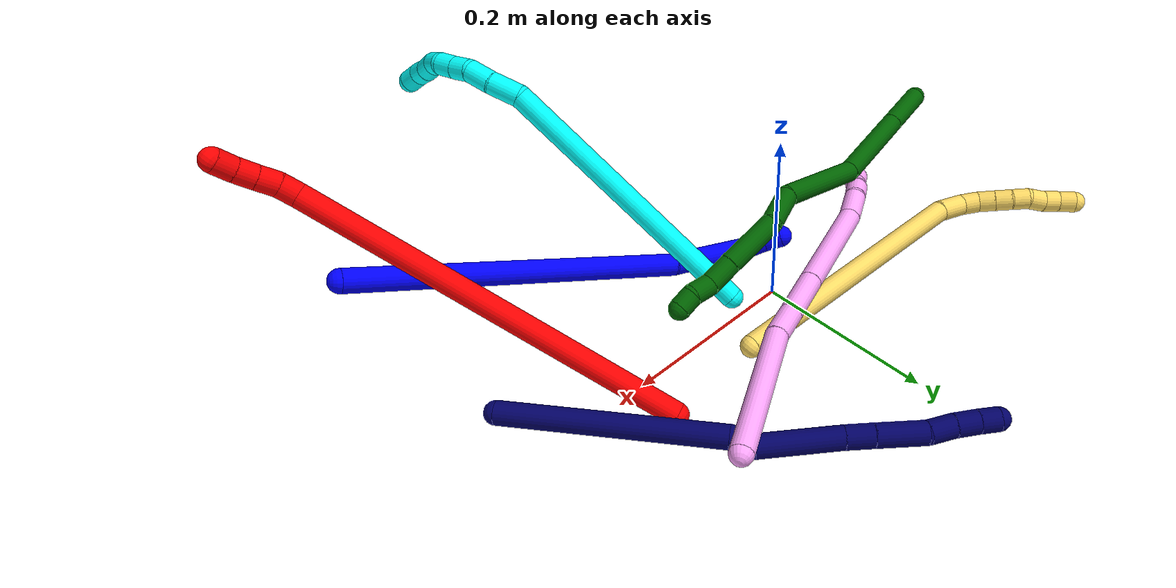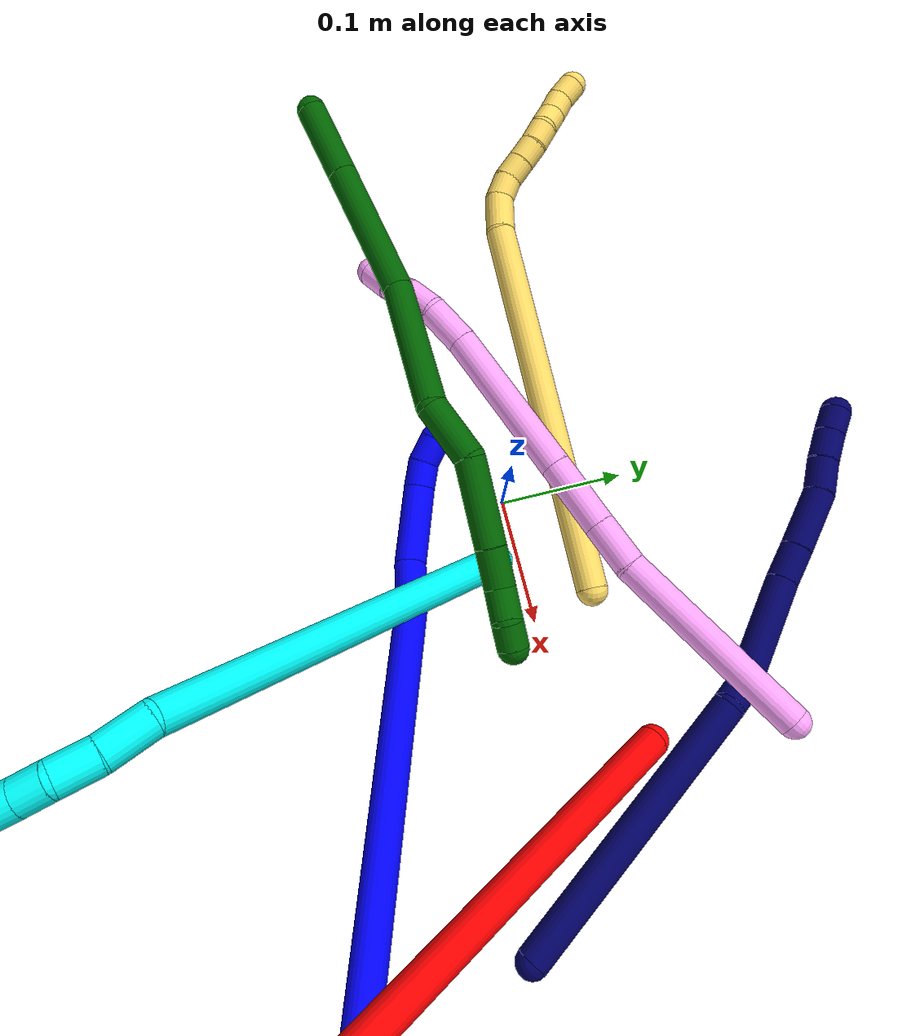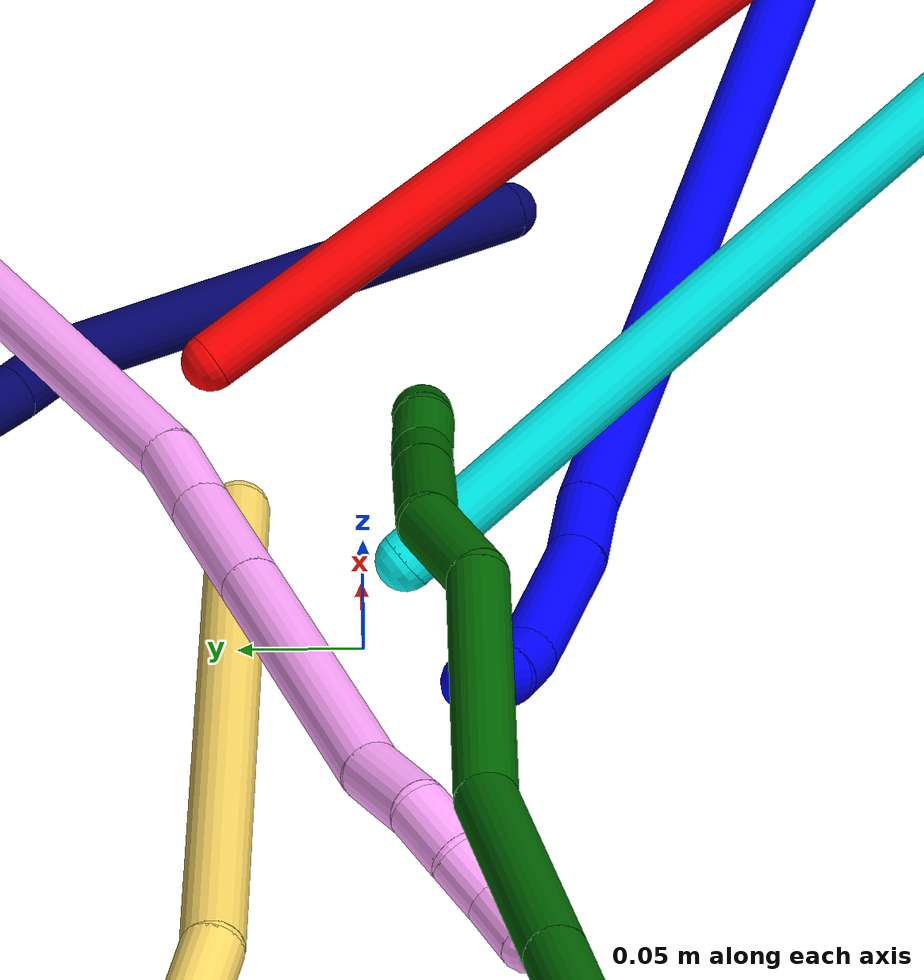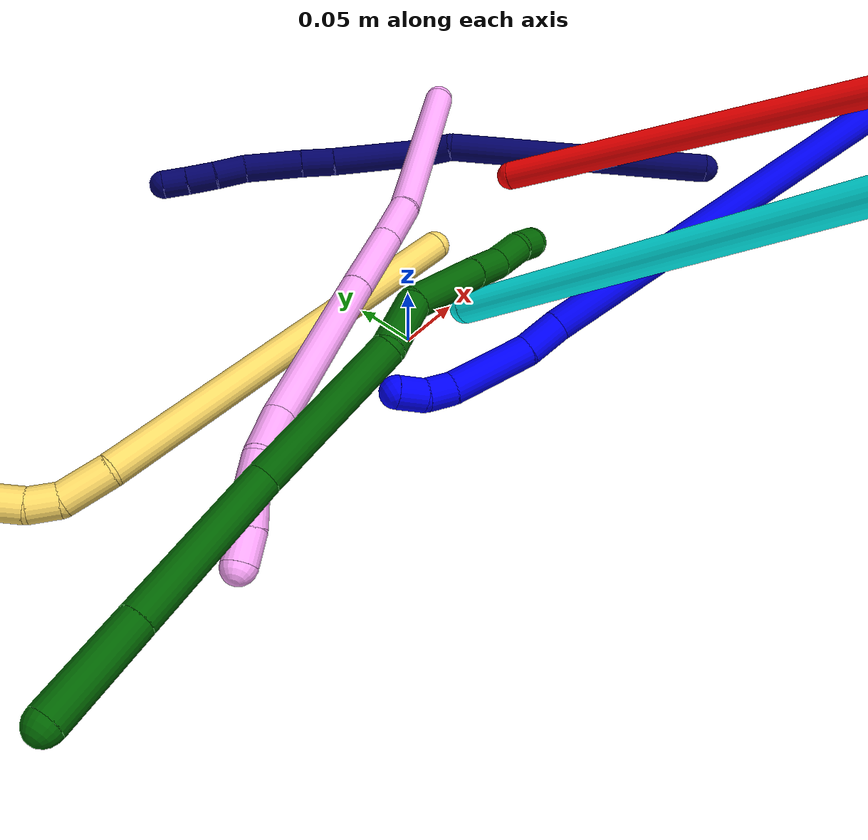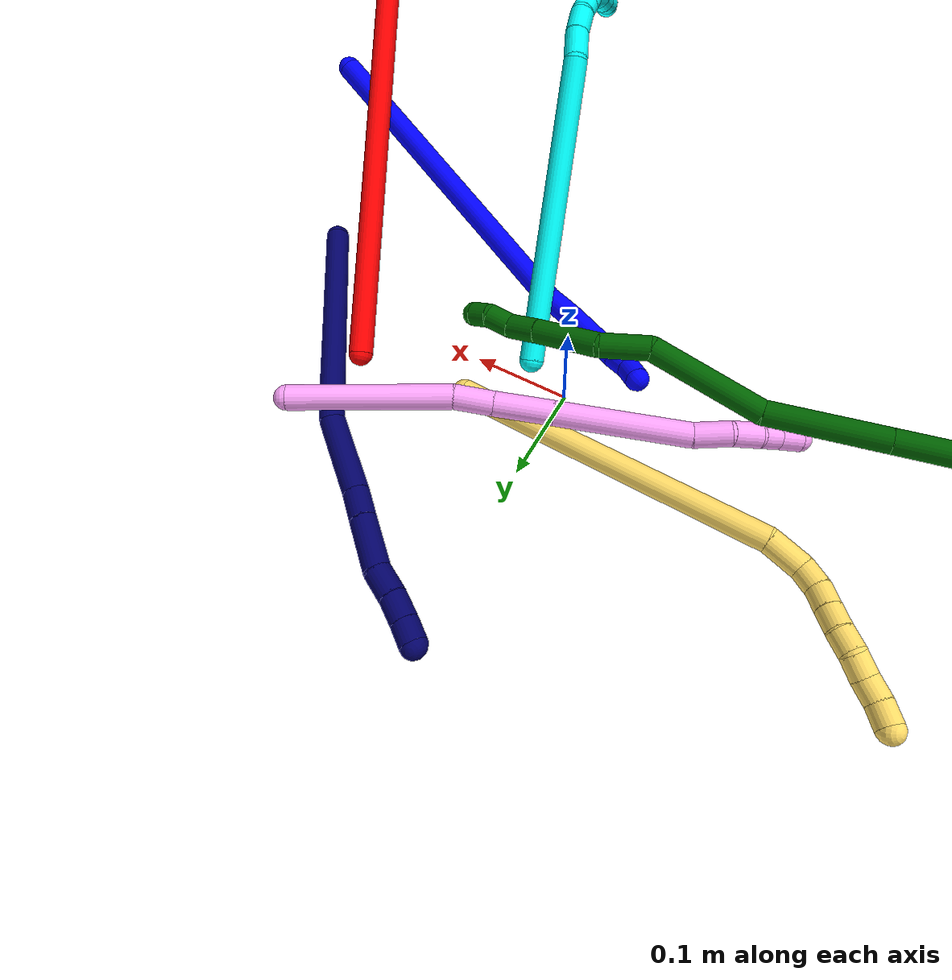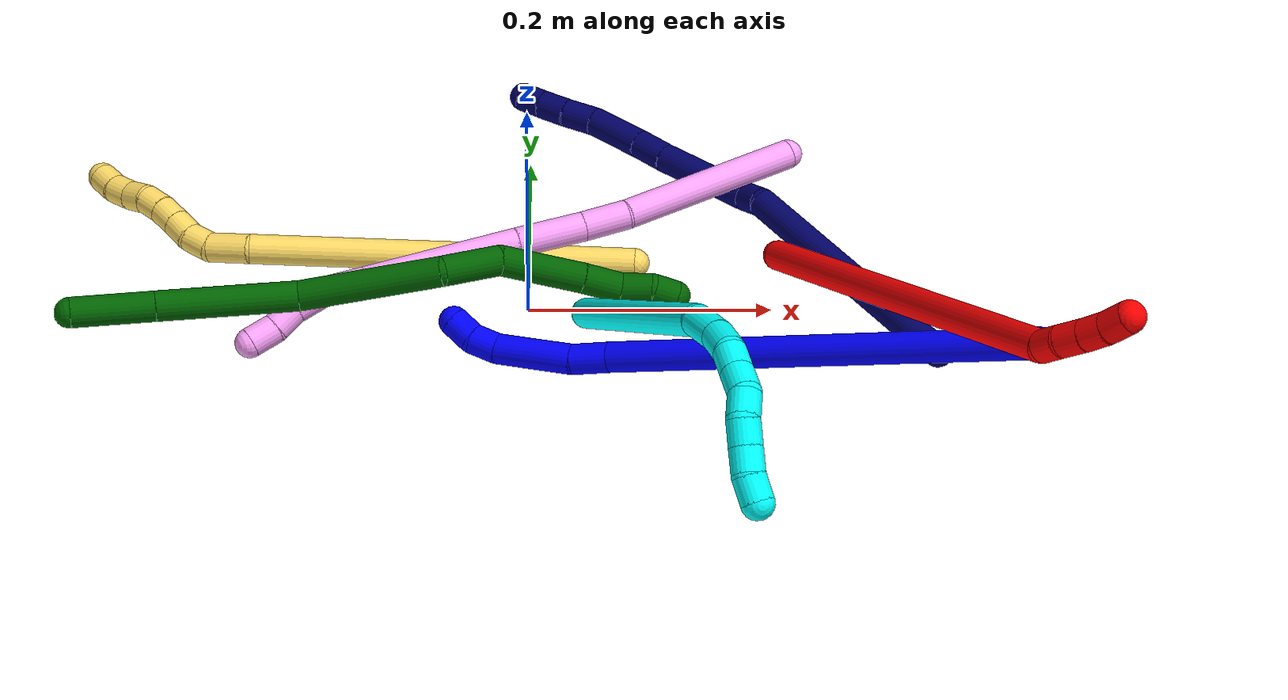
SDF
<sdf version="1.7">
 <world name="default">
  <plugin name="TubeGeneratorPlugin" filename="libtube_generator_plugin.so"/>
  <model name="photoneo_s_sensor">
   <static>1</static>
   <pose>0 0 2 1.57079 1.57079 3.14159</pose>
   <link name="link">
    <inertial><mass>0.1</mass></inertial>
    <sensor name="sensor" type="depth">
     <update_rate>30</update_rate>
     <camera>
      <horizontal_fov>1.22</horizontal_fov>
      <image><width>1920</width><height>1200</height><format>B8G8R8</format></image>
      <clip><near>0.1</near><far>4</far></clip>
      <depth_camera><output>points</output></depth_camera>
     </camera>
     <plugin name="camera_plugin" filename="libgazebo_ros_depth_camera.so">
      <baseline>0.2</baseline>
      <alwaysOn>1</alwaysOn>
      <updateRate>0.0</updateRate>
      <cameraName>camera_ir</cameraName>
      <imageTopicName>/camera/color/image_raw</imageTopicName>
      <cameraInfoTopicName>/camera/color/camera_info</cameraInfoTopicName>
      <depthImageTopicName>/camera/depth/image_raw</depthImageTopicName>
      <depthImageCameraInfoTopicName>/camera/depth/camera_info</depthImageCameraInfoTopicName>
      <pointCloudTopicName>/camera/depth/points</pointCloudTopicName>
      <frameName>fr_optical</frameName>
      <pointCloudCutoff>0.1</pointCloudCutoff>
      <pointCloudCutoffMax>2.0</pointCloudCutoffMax>
      <distortionK1>0</distortionK1>
      <distortionK2>0</distortionK2>
      <distortionK3>0</distortionK3>
      <distortionT1>0</distortionT1>
      <distortionT2>0</distortionT2>
      <CxPrime>0</CxPrime>
      <Cx>0</Cx>
      <Cy>0</Cy>
      <focalLength>0</focalLength>
      <hackBaseline>0</hackBaseline>
     </plugin>
    </sensor>
   </link>
  </model>
  <gravity>0 0 -9.8</gravity>
  <magnetic_field>6e-06 2.3e-05 -4.2e-05</magnetic_field>
  <atmosphere type="adiabatic"/>
  <physics name="default_physics" default="0" type="ode">
   <max_step_size>0.003</max_step_size>
   <real_time_factor>1</real_time_factor>
   <real_time_update_rate>1000</real_time_update_rate>
   <max_contacts>10000</max_contacts>
   <ode>
    <solver>
     <type>quick</type>
     <iters>100</iters>
     <sor>1.3</sor>
     <use_dynamic_moi_rescaling>0</use_dynamic_moi_rescaling>
    </solver>
    <constraints>
     <contact_max_correcting_vel>0</contact_max_correcting_vel>
     <contact_surface_layer>0.001</contact_surface_layer>
     <cfm>0</cfm>
     <erp>0.2</erp>
    </constraints>
   </ode>
  </physics>
  <scene><ambient>0.4 0.4 0.4 1</ambient><background>0.7 0.7 0.7 1</background><shadows>0</shadows></scene>
  <audio><device>default</device></audio>
  <spherical_coordinates>
   <surface_model>EARTH_WGS84</surface_model>
   <latitude_deg>0</latitude_deg>
   <longitude_deg>0</longitude_deg>
   <elevation>0</elevation>
   <heading_deg>0</heading_deg>
  </spherical_coordinates>
  <model name="bin">
   <static>1</static>
   <link name="bottom">
    <collision name="collision-bottom">
     <pose>0 0 -0.01 0 -0 0</pose>
     <geometry><box><size>0.8 0.6 0.02</size></box></geometry>
     <surface>
      <friction><ode><mu>100</mu><mu2>100</mu2></ode></friction>
      <contact><collide_bitmask>65535</collide_bitmask></contact>
     </surface>
    </collision>
   </link>
   <link name="west_wall">
    <collision name="collision-west_wall">
     <pose>-0.41 0 0.1 0 -0 0</pose>
     <geometry><box><size>0.02 0.6 0.2</size></box></geometry>
     <surface>
      <friction><ode><mu>100</mu><mu2>100</mu2></ode></friction>
      <contact><collide_bitmask>65535</collide_bitmask></contact>
     </surface>
    </collision>
   </link>
   <link name="east_wall">
    <collision name="collision-east_wall">
     <pose>0.41 0 0.1 0 -0 0</pose>
     <geometry><box><size>0.02 0.6 0.2</size></box></geometry>
     <surface>
      <friction><ode><mu>100</mu><mu2>100</mu2></ode></friction>
      <contact><collide_bitmask>65535</collide_bitmask></contact>
     </surface>
    </collision>
   </link>
   <link name="south_wall">
    <collision name="collision-south_wall">
     <pose>0 -0.31 0.1 0 -0 0</pose>
     <geometry><box><size>0.8 0.02 0.2</size></box></geometry>
     <surface>
      <friction><ode><mu>100</mu><mu2>100</mu2></ode></friction>
      <contact><collide_bitmask>65535</collide_bitmask></contact>
     </surface>
    </collision>
   </link>
   <link name="north_wall">
    <collision name="collision-north_wall">
     <pose>0 0.31 0.1 0 -0 0</pose>
     <geometry><box><size>0.8 0.02 0.2</size></box></geometry>
     <surface>
      <friction><ode><mu>100</mu><mu2>100</mu2></ode></friction>
      <contact><collide_bitmask>65535</collide_bitmask></contact>
     </surface>
    </collision>
   </link>
  </model>
  <model name="1">
   <static>0</static>
   <link name="1">
    <collision name="collision-cylinder-e_1_1_4">
     <pose>0.009086 -0.011047 -0.179325 3.08007 0.050527 1.37501</pose>
     <geometry><cylinder><radius>0.0125</radius><length>0.359789</length></cylinder></geometry>
     <surface>
      <friction><ode><mu>1.16</mu><mu2>1.16</mu2><slip1>0</slip1><slip2>0</slip2></ode></friction>
      <contact><ode><kp>1e+06</kp><kd>1</kd><max_vel>0</max_vel><min_depth>0.001</min_depth></ode></contact>
     </surface>
    </collision>
    <visual name="visual-cylinder-e_1_1_4">
     <pose>0.009086 -0.011047 -0.179325 3.08007 0.050527 1.37501</pose>
     <geometry><cylinder><radius>0.0125</radius><length>0.359789</length></cylinder></geometry>
     <material><ambient>0 0 1 1</ambient></material>
    </visual>
    <collision name="collision-cylinder-e_2_4_5">
     <pose>0.016795 -0.024653 -0.374058 2.97701 -0.087926 -0.979956</pose>
     <geometry><cylinder><radius>0.0125</radius><length>0.031358</length></cylinder></geometry>
     <surface>
      <friction><ode><mu>1.16</mu><mu2>1.16</mu2><slip1>0</slip1><slip2>0</slip2></ode></friction>
      <contact><ode><kp>1e+06</kp><kd>1</kd><max_vel>0</max_vel><min_depth>0.001</min_depth></ode></contact>
     </surface>
    </collision>
    <visual name="visual-cylinder-e_2_4_5">
     <pose>0.016795 -0.024653 -0.374058 2.97701 -0.087926 -0.979956</pose>
     <geometry><cylinder><radius>0.0125</radius><length>0.031358</length></cylinder></geometry>
     <material><ambient>0 0 1 1</ambient></material>
    </visual>
    <collision name="collision-cylinder-e_3_5_6">
     <pose>0.011203 -0.026225 -0.42165 -3.11094 -0.130162 2.67957</pose>
     <geometry><cylinder><radius>0.0125</radius><length>0.064948</length></cylinder></geometry>
     <surface>
      <friction><ode><mu>1.16</mu><mu2>1.16</mu2><slip1>0</slip1><slip2>0</slip2></ode></friction>
      <contact><ode><kp>1e+06</kp><kd>1</kd><max_vel>0</max_vel><min_depth>0.001</min_depth></ode></contact>
     </surface>
    </collision>
    <visual name="visual-cylinder-e_3_5_6">
     <pose>0.011203 -0.026225 -0.42165 -3.11094 -0.130162 2.67957</pose>
     <geometry><cylinder><radius>0.0125</radius><length>0.064948</length></cylinder></geometry>
     <material><ambient>0 0 1 1</ambient></material>
    </visual>
    <collision name="collision-cylinder-e_4_6_7">
     <pose>0.003357 -0.023067 -0.464026 -2.93167 -0.335303 2.02802</pose>
     <geometry><cylinder><radius>0.0125</radius><length>0.02207</length></cylinder></geometry>
     <surface>
      <friction><ode><mu>1.16</mu><mu2>1.16</mu2><slip1>0</slip1><slip2>0</slip2></ode></friction>
      <contact><ode><kp>1e+06</kp><kd>1</kd><max_vel>0</max_vel><min_depth>0.001</min_depth></ode></contact>
     </surface>
    </collision>
    <visual name="visual-cylinder-e_4_6_7">
     <pose>0.003357 -0.023067 -0.464026 -2.93167 -0.335303 2.02802</pose>
     <geometry><cylinder><radius>0.0125</radius><length>0.02207</length></cylinder></geometry>
     <material><ambient>0 0 1 1</ambient></material>
    </visual>
    <collision name="collision-cylinder-e_5_7_2">
     <pose>-0.003703 -0.015152 -0.482846 -2.55432 -0.319427 0.978979</pose>
     <geometry><cylinder><radius>0.0125</radius><length>0.021833</length></cylinder></geometry>
     <surface>
      <friction><ode><mu>1.16</mu><mu2>1.16</mu2><slip1>0</slip1><slip2>0</slip2></ode></friction>
      <contact><ode><kp>1e+06</kp><kd>1</kd><max_vel>0</max_vel><min_depth>0.001</min_depth></ode></contact>
     </surface>
    </collision>
    <visual name="visual-cylinder-e_5_7_2">
     <pose>-0.003703 -0.015152 -0.482846 -2.55432 -0.319427 0.978979</pose>
     <geometry><cylinder><radius>0.0125</radius><length>0.021833</length></cylinder></geometry>
     <material><ambient>0 0 1 1</ambient></material>
    </visual>
    <collision name="collision-sphere-2">
     <pose>-0.007131 -0.00941 -0.491474 0 -0 0</pose>
     <geometry><sphere><radius>0.0125</radius></sphere></geometry>
     <surface>
      <friction><ode><mu>1.16</mu><mu2>1.16</mu2><slip1>0</slip1><slip2>0</slip2></ode></friction>
      <contact><ode><kp>1e+06</kp><kd>1</kd><max_vel>0</max_vel><min_depth>0.001</min_depth></ode></contact>
     </surface>
    </collision>
    <visual name="visual-sphere-2">
     <pose>-0.007131 -0.00941 -0.491474 0 -0 0</pose>
     <geometry><sphere><radius>0.0125</radius></sphere></geometry>
     <material><ambient>0 0 1 1</ambient></material>
    </visual>
    <collision name="collision-sphere-7">
     <pose>-0.000275 -0.020895 -0.474218 0 -0 0</pose>
     <geometry><sphere><radius>0.0125</radius></sphere></geometry>
     <surface>
      <friction><ode><mu>1.16</mu><mu2>1.16</mu2><slip1>0</slip1><slip2>0</slip2></ode></friction>
      <contact><ode><kp>1e+06</kp><kd>1</kd><max_vel>0</max_vel><min_depth>0.001</min_depth></ode></contact>
     </surface>
    </collision>
    <visual name="visual-sphere-7">
     <pose>-0.000275 -0.020895 -0.474218 0 -0 0</pose>
     <geometry><sphere><radius>0.0125</radius></sphere></geometry>
     <material><ambient>0 0 1 1</ambient></material>
    </visual>
    <collision name="collision-sphere-6">
     <pose>0.006988 -0.025238 -0.453834 0 -0 0</pose>
     <geometry><sphere><radius>0.0125</radius></sphere></geometry>
     <surface>
      <friction><ode><mu>1.16</mu><mu2>1.16</mu2><slip1>0</slip1><slip2>0</slip2></ode></friction>
      <contact><ode><kp>1e+06</kp><kd>1</kd><max_vel>0</max_vel><min_depth>0.001</min_depth></ode></contact>
     </surface>
    </collision>
    <visual name="visual-sphere-6">
     <pose>0.006988 -0.025238 -0.453834 0 -0 0</pose>
     <geometry><sphere><radius>0.0125</radius></sphere></geometry>
     <material><ambient>0 0 1 1</ambient></material>
    </visual>
    <collision name="collision-sphere-5">
     <pose>0.015418 -0.027212 -0.389466 0 -0 0</pose>
     <geometry><sphere><radius>0.0125</radius></sphere></geometry>
     <surface>
      <friction><ode><mu>1.16</mu><mu2>1.16</mu2><slip1>0</slip1><slip2>0</slip2></ode></friction>
      <contact><ode><kp>1e+06</kp><kd>1</kd><max_vel>0</max_vel><min_depth>0.001</min_depth></ode></contact>
     </surface>
    </collision>
    <visual name="visual-sphere-5">
     <pose>0.015418 -0.027212 -0.389466 0 -0 0</pose>
     <geometry><sphere><radius>0.0125</radius></sphere></geometry>
     <material><ambient>0 0 1 1</ambient></material>
    </visual>
    <collision name="collision-sphere-1">
     <geometry><sphere><radius>0.0125</radius></sphere></geometry>
     <surface>
      <friction><ode><mu>1.16</mu><mu2>1.16</mu2><slip1>0</slip1><slip2>0</slip2></ode></friction>
      <contact><ode><kp>1e+06</kp><kd>1</kd><max_vel>0</max_vel><min_depth>0.001</min_depth></ode></contact>
     </surface>
    </collision>
    <visual name="visual-sphere-1">
     <geometry><sphere><radius>0.0125</radius></sphere></geometry>
     <material><ambient>0 0 1 1</ambient></material>
    </visual>
    <collision name="collision-sphere-4">
     <pose>0.018171 -0.022094 -0.35865 0 -0 0</pose>
     <geometry><sphere><radius>0.0125</radius></sphere></geometry>
     <surface>
      <friction><ode><mu>1.16</mu><mu2>1.16</mu2><slip1>0</slip1><slip2>0</slip2></ode></friction>
      <contact><ode><kp>1e+06</kp><kd>1</kd><max_vel>0</max_vel><min_depth>0.001</min_depth></ode></contact>
     </surface>
    </collision>
    <visual name="visual-sphere-4">
     <pose>0.018171 -0.022094 -0.35865 0 -0 0</pose>
     <geometry><sphere><radius>0.0125</radius></sphere></geometry>
     <material><ambient>0 0 1 1</ambient></material>
    </visual>
    <inertial>
     <pose>0.009033 -0.014582 -0.248836 0 -0 0</pose>
     <mass>0.5</mass>
     <inertia><ixx>0.004563</ixx><ixy>0</ixy><ixz>0</ixz><iyy>0.003103</iyy><iyz>0</iyz><izz>7e-06</izz></inertia>
    </inertial>
   </link>
   <pose>0.388502 -0.206748 0.135936 1.07061 1.0546 0.749108</pose>
  </model>
  <model name="2">
   <static>0</static>
   <link name="2">
    <collision name="collision-cylinder-e_1_1_4">
     <pose>0.004488 -0.027107 0.20722 0.130074 0.02147 0.001398</pose>
     <geometry><cylinder><radius>0.0125</radius><length>0.418067</length></cylinder></geometry>
     <surface>
      <friction><ode><mu>1.16</mu><mu2>1.16</mu2><slip1>0</slip1><slip2>0</slip2></ode></friction>
      <contact><ode><kp>1e+06</kp><kd>1</kd><max_vel>0</max_vel><min_depth>0.001</min_depth></ode></contact>
     </surface>
    </collision>
    <visual name="visual-cylinder-e_1_1_4">
     <pose>0.004488 -0.027107 0.20722 0.130074 0.02147 0.001398</pose>
     <geometry><cylinder><radius>0.0125</radius><length>0.418067</length></cylinder></geometry>
     <material><ambient>1 0 0 1</ambient></material>
    </visual>
    <collision name="collision-cylinder-e_2_4_5">
     <pose>0.012888 -0.057069 0.423454 0.306754 0.392372 0.061428</pose>
     <geometry><cylinder><radius>0.0125</radius><length>0.020465</length></cylinder></geometry>
     <surface>
      <friction><ode><mu>1.16</mu><mu2>1.16</mu2><slip1>0</slip1><slip2>0</slip2></ode></friction>
      <contact><ode><kp>1e+06</kp><kd>1</kd><max_vel>0</max_vel><min_depth>0.001</min_depth></ode></contact>
     </surface>
    </collision>
    <visual name="visual-cylinder-e_2_4_5">
     <pose>0.012888 -0.057069 0.423454 0.306754 0.392372 0.061428</pose>
     <geometry><cylinder><radius>0.0125</radius><length>0.020465</length></cylinder></geometry>
     <material><ambient>1 0 0 1</ambient></material>
    </visual>
    <collision name="collision-cylinder-e_3_5_6">
     <pose>0.021003 -0.064929 0.440774 0.542213 0.408927 0.115145</pose>
     <geometry><cylinder><radius>0.0125</radius><length>0.021139</length></cylinder></geometry>
     <surface>
      <friction><ode><mu>1.16</mu><mu2>1.16</mu2><slip1>0</slip1><slip2>0</slip2></ode></friction>
      <contact><ode><kp>1e+06</kp><kd>1</kd><max_vel>0</max_vel><min_depth>0.001</min_depth></ode></contact>
     </surface>
    </collision>
    <visual name="visual-cylinder-e_3_5_6">
     <pose>0.021003 -0.064929 0.440774 0.542213 0.408927 0.115145</pose>
     <geometry><cylinder><radius>0.0125</radius><length>0.021139</length></cylinder></geometry>
     <material><ambient>1 0 0 1</ambient></material>
    </visual>
    <collision name="collision-cylinder-e_4_6_7">
     <pose>0.029694 -0.074504 0.456784 0.53561 0.46452 0.129624</pose>
     <geometry><cylinder><radius>0.0125</radius><length>0.020038</length></cylinder></geometry>
     <surface>
      <friction><ode><mu>1.16</mu><mu2>1.16</mu2><slip1>0</slip1><slip2>0</slip2></ode></friction>
      <contact><ode><kp>1e+06</kp><kd>1</kd><max_vel>0</max_vel><min_depth>0.001</min_depth></ode></contact>
     </surface>
    </collision>
    <visual name="visual-cylinder-e_4_6_7">
     <pose>0.029694 -0.074504 0.456784 0.53561 0.46452 0.129624</pose>
     <geometry><cylinder><radius>0.0125</radius><length>0.020038</length></cylinder></geometry>
     <material><ambient>1 0 0 1</ambient></material>
    </visual>
    <collision name="collision-cylinder-e_5_7_2">
     <pose>0.039798 -0.083206 0.471858 0.510647 0.586536 0.157318</pose>
     <geometry><cylinder><radius>0.0125</radius><length>0.020291</length></cylinder></geometry>
     <surface>
      <friction><ode><mu>1.16</mu><mu2>1.16</mu2><slip1>0</slip1><slip2>0</slip2></ode></friction>
      <contact><ode><kp>1e+06</kp><kd>1</kd><max_vel>0</max_vel><min_depth>0.001</min_depth></ode></contact>
     </surface>
    </collision>
    <visual name="visual-cylinder-e_5_7_2">
     <pose>0.039798 -0.083206 0.471858 0.510647 0.586536 0.157318</pose>
     <geometry><cylinder><radius>0.0125</radius><length>0.020291</length></cylinder></geometry>
     <material><ambient>1 0 0 1</ambient></material>
    </visual>
    <collision name="collision-sphere-2">
     <pose>0.045413 -0.087336 0.47923 0 -0 0</pose>
     <geometry><sphere><radius>0.0125</radius></sphere></geometry>
     <surface>
      <friction><ode><mu>1.16</mu><mu2>1.16</mu2><slip1>0</slip1><slip2>0</slip2></ode></friction>
      <contact><ode><kp>1e+06</kp><kd>1</kd><max_vel>0</max_vel><min_depth>0.001</min_depth></ode></contact>
     </surface>
    </collision>
    <visual name="visual-sphere-2">
     <pose>0.045413 -0.087336 0.47923 0 -0 0</pose>
     <geometry><sphere><radius>0.0125</radius></sphere></geometry>
     <material><ambient>1 0 0 1</ambient></material>
    </visual>
    <collision name="collision-sphere-7">
     <pose>0.034183 -0.079076 0.464486 0 -0 0</pose>
     <geometry><sphere><radius>0.0125</radius></sphere></geometry>
     <surface>
      <friction><ode><mu>1.16</mu><mu2>1.16</mu2><slip1>0</slip1><slip2>0</slip2></ode></friction>
      <contact><ode><kp>1e+06</kp><kd>1</kd><max_vel>0</max_vel><min_depth>0.001</min_depth></ode></contact>
     </surface>
    </collision>
    <visual name="visual-sphere-7">
     <pose>0.034183 -0.079076 0.464486 0 -0 0</pose>
     <geometry><sphere><radius>0.0125</radius></sphere></geometry>
     <material><ambient>1 0 0 1</ambient></material>
    </visual>
    <collision name="collision-sphere-6">
     <pose>0.025206 -0.069933 0.449081 0 -0 0</pose>
     <geometry><sphere><radius>0.0125</radius></sphere></geometry>
     <surface>
      <friction><ode><mu>1.16</mu><mu2>1.16</mu2><slip1>0</slip1><slip2>0</slip2></ode></friction>
      <contact><ode><kp>1e+06</kp><kd>1</kd><max_vel>0</max_vel><min_depth>0.001</min_depth></ode></contact>
     </surface>
    </collision>
    <visual name="visual-sphere-6">
     <pose>0.025206 -0.069933 0.449081 0 -0 0</pose>
     <geometry><sphere><radius>0.0125</radius></sphere></geometry>
     <material><ambient>1 0 0 1</ambient></material>
    </visual>
    <collision name="collision-sphere-5">
     <pose>0.0168 -0.059924 0.432467 0 -0 0</pose>
     <geometry><sphere><radius>0.0125</radius></sphere></geometry>
     <surface>
      <friction><ode><mu>1.16</mu><mu2>1.16</mu2><slip1>0</slip1><slip2>0</slip2></ode></friction>
      <contact><ode><kp>1e+06</kp><kd>1</kd><max_vel>0</max_vel><min_depth>0.001</min_depth></ode></contact>
     </surface>
    </collision>
    <visual name="visual-sphere-5">
     <pose>0.0168 -0.059924 0.432467 0 -0 0</pose>
     <geometry><sphere><radius>0.0125</radius></sphere></geometry>
     <material><ambient>1 0 0 1</ambient></material>
    </visual>
    <collision name="collision-sphere-1">
     <geometry><sphere><radius>0.0125</radius></sphere></geometry>
     <surface>
      <friction><ode><mu>1.16</mu><mu2>1.16</mu2><slip1>0</slip1><slip2>0</slip2></ode></friction>
      <contact><ode><kp>1e+06</kp><kd>1</kd><max_vel>0</max_vel><min_depth>0.001</min_depth></ode></contact>
     </surface>
    </collision>
    <visual name="visual-sphere-1">
     <geometry><sphere><radius>0.0125</radius></sphere></geometry>
     <material><ambient>1 0 0 1</ambient></material>
    </visual>
    <collision name="collision-sphere-4">
     <pose>0.008975 -0.054214 0.41444 0 -0 0</pose>
     <geometry><sphere><radius>0.0125</radius></sphere></geometry>
     <surface>
      <friction><ode><mu>1.16</mu><mu2>1.16</mu2><slip1>0</slip1><slip2>0</slip2></ode></friction>
      <contact><ode><kp>1e+06</kp><kd>1</kd><max_vel>0</max_vel><min_depth>0.001</min_depth></ode></contact>
     </surface>
    </collision>
    <visual name="visual-sphere-4">
     <pose>0.008975 -0.054214 0.41444 0 -0 0</pose>
     <geometry><sphere><radius>0.0125</radius></sphere></geometry>
     <material><ambient>1 0 0 1</ambient></material>
    </visual>
    <inertial>
     <pose>0.007973 -0.034109 0.246686 0 -0 0</pose>
     <mass>0.5</mass>
     <inertia>
      <ixx>0.006122</ixx>
      <ixy>0</ixy>
      <ixz>0</ixz>
      <iyy>0.006062</iyy>
      <iyz>0</iyz>
      <izz>0.000698</izz>
     </inertia>
    </inertial>
   </link>
   <pose>0.208337 0.059634 0.011497 0.478392 -1.04318 1.34415</pose>
  </model>
  <model name="3">
   <static>0</static>
   <link name="3">
    <collision name="collision-cylinder-e_1_1_4">
     <pose>-0.009658 -0.007626 0.15699 0.048537 -0.061371 -0.00149</pose>
     <geometry><cylinder><radius>0.0125</radius><length>0.314942</length></cylinder></geometry>
     <surface>
      <friction><ode><mu>1.16</mu><mu2>1.16</mu2><slip1>0</slip1><slip2>0</slip2></ode></friction>
      <contact><ode><kp>1e+06</kp><kd>1</kd><max_vel>0</max_vel><min_depth>0.001</min_depth></ode></contact>
     </surface>
    </collision>
    <visual name="visual-cylinder-e_1_1_4">
     <pose>-0.009658 -0.007626 0.15699 0.048537 -0.061371 -0.00149</pose>
     <geometry><cylinder><radius>0.0125</radius><length>0.314942</length></cylinder></geometry>
     <material><ambient>0.003922 1 0.996078 1</ambient></material>
    </visual>
    <collision name="collision-cylinder-e_2_4_5">
     <pose>-0.015285 -0.012621 0.330476 -0.158149 0.236777 -0.01885</pose>
     <geometry><cylinder><radius>0.0125</radius><length>0.03437</length></cylinder></geometry>
     <surface>
      <friction><ode><mu>1.16</mu><mu2>1.16</mu2><slip1>0</slip1><slip2>0</slip2></ode></friction>
      <contact><ode><kp>1e+06</kp><kd>1</kd><max_vel>0</max_vel><min_depth>0.001</min_depth></ode></contact>
     </surface>
    </collision>
    <visual name="visual-cylinder-e_2_4_5">
     <pose>-0.015285 -0.012621 0.330476 -0.158149 0.236777 -0.01885</pose>
     <geometry><cylinder><radius>0.0125</radius><length>0.03437</length></cylinder></geometry>
     <material><ambient>0.003922 1 0.996078 1</ambient></material>
    </visual>
    <collision name="collision-cylinder-e_3_5_6">
     <pose>-0.006812 -0.009717 0.360269 -0.020497 0.322386 -0.003333</pose>
     <geometry><cylinder><radius>0.0125</radius><length>0.028042</length></cylinder></geometry>
     <surface>
      <friction><ode><mu>1.16</mu><mu2>1.16</mu2><slip1>0</slip1><slip2>0</slip2></ode></friction>
      <contact><ode><kp>1e+06</kp><kd>1</kd><max_vel>0</max_vel><min_depth>0.001</min_depth></ode></contact>
     </surface>
    </collision>
    <visual name="visual-cylinder-e_3_5_6">
     <pose>-0.006812 -0.009717 0.360269 -0.020497 0.322386 -0.003333</pose>
     <geometry><cylinder><radius>0.0125</radius><length>0.028042</length></cylinder></geometry>
     <material><ambient>0.003922 1 0.996078 1</ambient></material>
    </visual>
    <collision name="collision-cylinder-e_4_6_7">
     <pose>0.004327 -0.008712 0.381431 -0.092811 0.703101 -0.034063</pose>
     <geometry><cylinder><radius>0.0125</radius><length>0.020712</length></cylinder></geometry>
     <surface>
      <friction><ode><mu>1.16</mu><mu2>1.16</mu2><slip1>0</slip1><slip2>0</slip2></ode></friction>
      <contact><ode><kp>1e+06</kp><kd>1</kd><max_vel>0</max_vel><min_depth>0.001</min_depth></ode></contact>
     </surface>
    </collision>
    <visual name="visual-cylinder-e_4_6_7">
     <pose>0.004327 -0.008712 0.381431 -0.092811 0.703101 -0.034063</pose>
     <geometry><cylinder><radius>0.0125</radius><length>0.020712</length></cylinder></geometry>
     <material><ambient>0.003922 1 0.996078 1</ambient></material>
    </visual>
    <collision name="collision-cylinder-e_5_7_8">
     <pose>0.017532 -0.007441 0.397811 -0.06326 0.651766 -0.021384</pose>
     <geometry><cylinder><radius>0.0125</radius><length>0.021461</length></cylinder></geometry>
     <surface>
      <friction><ode><mu>1.16</mu><mu2>1.16</mu2><slip1>0</slip1><slip2>0</slip2></ode></friction>
      <contact><ode><kp>1e+06</kp><kd>1</kd><max_vel>0</max_vel><min_depth>0.001</min_depth></ode></contact>
     </surface>
    </collision>
    <visual name="visual-cylinder-e_5_7_8">
     <pose>0.017532 -0.007441 0.397811 -0.06326 0.651766 -0.021384</pose>
     <geometry><cylinder><radius>0.0125</radius><length>0.021461</length></cylinder></geometry>
     <material><ambient>0.003922 1 0.996078 1</ambient></material>
    </visual>
    <collision name="collision-cylinder-e_6_8_9">
     <pose>0.03263 -0.008423 0.411302 0.296578 1.02609 0.167922</pose>
     <geometry><cylinder><radius>0.0125</radius><length>0.020085</length></cylinder></geometry>
     <surface>
      <friction><ode><mu>1.16</mu><mu2>1.16</mu2><slip1>0</slip1><slip2>0</slip2></ode></friction>
      <contact><ode><kp>1e+06</kp><kd>1</kd><max_vel>0</max_vel><min_depth>0.001</min_depth></ode></contact>
     </surface>
    </collision>
    <visual name="visual-cylinder-e_6_8_9">
     <pose>0.03263 -0.008423 0.411302 0.296578 1.02609 0.167922</pose>
     <geometry><cylinder><radius>0.0125</radius><length>0.020085</length></cylinder></geometry>
     <material><ambient>0.003922 1 0.996078 1</ambient></material>
    </visual>
    <collision name="collision-cylinder-e_7_9_10">
     <pose>0.050923 -0.008819 0.418895 -0.405757 1.28534 -0.305626</pose>
     <geometry><cylinder><radius>0.0125</radius><length>0.020226</length></cylinder></geometry>
     <surface>
      <friction><ode><mu>1.16</mu><mu2>1.16</mu2><slip1>0</slip1><slip2>0</slip2></ode></friction>
      <contact><ode><kp>1e+06</kp><kd>1</kd><max_vel>0</max_vel><min_depth>0.001</min_depth></ode></contact>
     </surface>
    </collision>
    <visual name="visual-cylinder-e_7_9_10">
     <pose>0.050923 -0.008819 0.418895 -0.405757 1.28534 -0.305626</pose>
     <geometry><cylinder><radius>0.0125</radius><length>0.020226</length></cylinder></geometry>
     <material><ambient>0.003922 1 0.996078 1</ambient></material>
    </visual>
    <collision name="collision-cylinder-e_8_10_11">
     <pose>0.069905 -0.006944 0.425167 -0.202697 1.18834 -0.1372</pose>
     <geometry><cylinder><radius>0.0125</radius><length>0.020001</length></cylinder></geometry>
     <surface>
      <friction><ode><mu>1.16</mu><mu2>1.16</mu2><slip1>0</slip1><slip2>0</slip2></ode></friction>
      <contact><ode><kp>1e+06</kp><kd>1</kd><max_vel>0</max_vel><min_depth>0.001</min_depth></ode></contact>
     </surface>
    </collision>
    <visual name="visual-cylinder-e_8_10_11">
     <pose>0.069905 -0.006944 0.425167 -0.202697 1.18834 -0.1372</pose>
     <geometry><cylinder><radius>0.0125</radius><length>0.020001</length></cylinder></geometry>
     <material><ambient>0.003922 1 0.996078 1</ambient></material>
    </visual>
    <collision name="collision-cylinder-e_9_11_2">
     <pose>0.088215 -0.002954 0.431912 -0.808988 1.11076 -0.519306</pose>
     <geometry><cylinder><radius>0.0125</radius><length>0.02016</length></cylinder></geometry>
     <surface>
      <friction><ode><mu>1.16</mu><mu2>1.16</mu2><slip1>0</slip1><slip2>0</slip2></ode></friction>
      <contact><ode><kp>1e+06</kp><kd>1</kd><max_vel>0</max_vel><min_depth>0.001</min_depth></ode></contact>
     </surface>
    </collision>
    <visual name="visual-cylinder-e_9_11_2">
     <pose>0.088215 -0.002954 0.431912 -0.808988 1.11076 -0.519306</pose>
     <geometry><cylinder><radius>0.0125</radius><length>0.02016</length></cylinder></geometry>
     <material><ambient>0.003922 1 0.996078 1</ambient></material>
    </visual>
    <collision name="collision-sphere-2">
     <pose>0.097247 0.000284 0.435001 0 -0 0</pose>
     <geometry><sphere><radius>0.0125</radius></sphere></geometry>
     <surface>
      <friction><ode><mu>1.16</mu><mu2>1.16</mu2><slip1>0</slip1><slip2>0</slip2></ode></friction>
      <contact><ode><kp>1e+06</kp><kd>1</kd><max_vel>0</max_vel><min_depth>0.001</min_depth></ode></contact>
     </surface>
    </collision>
    <visual name="visual-sphere-2">
     <pose>0.097247 0.000284 0.435001 0 -0 0</pose>
     <geometry><sphere><radius>0.0125</radius></sphere></geometry>
     <material><ambient>0.003922 1 0.996078 1</ambient></material>
    </visual>
    <collision name="collision-sphere-11">
     <pose>0.079183 -0.006192 0.428823 0 -0 0</pose>
     <geometry><sphere><radius>0.0125</radius></sphere></geometry>
     <surface>
      <friction><ode><mu>1.16</mu><mu2>1.16</mu2><slip1>0</slip1><slip2>0</slip2></ode></friction>
      <contact><ode><kp>1e+06</kp><kd>1</kd><max_vel>0</max_vel><min_depth>0.001</min_depth></ode></contact>
     </surface>
    </collision>
    <visual name="visual-sphere-11">
     <pose>0.079183 -0.006192 0.428823 0 -0 0</pose>
     <geometry><sphere><radius>0.0125</radius></sphere></geometry>
     <material><ambient>0.003922 1 0.996078 1</ambient></material>
    </visual>
    <collision name="collision-sphere-10">
     <pose>0.060627 -0.007695 0.421511 0 -0 0</pose>
     <geometry><sphere><radius>0.0125</radius></sphere></geometry>
     <surface>
      <friction><ode><mu>1.16</mu><mu2>1.16</mu2><slip1>0</slip1><slip2>0</slip2></ode></friction>
      <contact><ode><kp>1e+06</kp><kd>1</kd><max_vel>0</max_vel><min_depth>0.001</min_depth></ode></contact>
     </surface>
    </collision>
    <visual name="visual-sphere-10">
     <pose>0.060627 -0.007695 0.421511 0 -0 0</pose>
     <geometry><sphere><radius>0.0125</radius></sphere></geometry>
     <material><ambient>0.003922 1 0.996078 1</ambient></material>
    </visual>
    <collision name="collision-sphere-9">
     <pose>0.041219 -0.009943 0.416278 0 -0 0</pose>
     <geometry><sphere><radius>0.0125</radius></sphere></geometry>
     <surface>
      <friction><ode><mu>1.16</mu><mu2>1.16</mu2><slip1>0</slip1><slip2>0</slip2></ode></friction>
      <contact><ode><kp>1e+06</kp><kd>1</kd><max_vel>0</max_vel><min_depth>0.001</min_depth></ode></contact>
     </surface>
    </collision>
    <visual name="visual-sphere-9">
     <pose>0.041219 -0.009943 0.416278 0 -0 0</pose>
     <geometry><sphere><radius>0.0125</radius></sphere></geometry>
     <material><ambient>0.003922 1 0.996078 1</ambient></material>
    </visual>
    <collision name="collision-sphere-4">
     <pose>-0.019316 -0.015252 0.313979 0 -0 0</pose>
     <geometry><sphere><radius>0.0125</radius></sphere></geometry>
     <surface>
      <friction><ode><mu>1.16</mu><mu2>1.16</mu2><slip1>0</slip1><slip2>0</slip2></ode></friction>
      <contact><ode><kp>1e+06</kp><kd>1</kd><max_vel>0</max_vel><min_depth>0.001</min_depth></ode></contact>
     </surface>
    </collision>
    <visual name="visual-sphere-4">
     <pose>-0.019316 -0.015252 0.313979 0 -0 0</pose>
     <geometry><sphere><radius>0.0125</radius></sphere></geometry>
     <material><ambient>0.003922 1 0.996078 1</ambient></material>
    </visual>
    <collision name="collision-sphere-1">
     <geometry><sphere><radius>0.0125</radius></sphere></geometry>
     <surface>
      <friction><ode><mu>1.16</mu><mu2>1.16</mu2><slip1>0</slip1><slip2>0</slip2></ode></friction>
      <contact><ode><kp>1e+06</kp><kd>1</kd><max_vel>0</max_vel><min_depth>0.001</min_depth></ode></contact>
     </surface>
    </collision>
    <visual name="visual-sphere-1">
     <geometry><sphere><radius>0.0125</radius></sphere></geometry>
     <material><ambient>0.003922 1 0.996078 1</ambient></material>
    </visual>
    <collision name="collision-sphere-8">
     <pose>0.024041 -0.006902 0.406325 0 -0 0</pose>
     <geometry><sphere><radius>0.0125</radius></sphere></geometry>
     <surface>
      <friction><ode><mu>1.16</mu><mu2>1.16</mu2><slip1>0</slip1><slip2>0</slip2></ode></friction>
      <contact><ode><kp>1e+06</kp><kd>1</kd><max_vel>0</max_vel><min_depth>0.001</min_depth></ode></contact>
     </surface>
    </collision>
    <visual name="visual-sphere-8">
     <pose>0.024041 -0.006902 0.406325 0 -0 0</pose>
     <geometry><sphere><radius>0.0125</radius></sphere></geometry>
     <material><ambient>0.003922 1 0.996078 1</ambient></material>
    </visual>
    <collision name="collision-sphere-5">
     <pose>-0.011254 -0.00999 0.346973 0 -0 0</pose>
     <geometry><sphere><radius>0.0125</radius></sphere></geometry>
     <surface>
      <friction><ode><mu>1.16</mu><mu2>1.16</mu2><slip1>0</slip1><slip2>0</slip2></ode></friction>
      <contact><ode><kp>1e+06</kp><kd>1</kd><max_vel>0</max_vel><min_depth>0.001</min_depth></ode></contact>
     </surface>
    </collision>
    <visual name="visual-sphere-5">
     <pose>-0.011254 -0.00999 0.346973 0 -0 0</pose>
     <geometry><sphere><radius>0.0125</radius></sphere></geometry>
     <material><ambient>0.003922 1 0.996078 1</ambient></material>
    </visual>
    <collision name="collision-sphere-6">
     <pose>-0.002369 -0.009445 0.373565 0 -0 0</pose>
     <geometry><sphere><radius>0.0125</radius></sphere></geometry>
     <surface>
      <friction><ode><mu>1.16</mu><mu2>1.16</mu2><slip1>0</slip1><slip2>0</slip2></ode></friction>
      <contact><ode><kp>1e+06</kp><kd>1</kd><max_vel>0</max_vel><min_depth>0.001</min_depth></ode></contact>
     </surface>
    </collision>
    <visual name="visual-sphere-6">
     <pose>-0.002369 -0.009445 0.373565 0 -0 0</pose>
     <geometry><sphere><radius>0.0125</radius></sphere></geometry>
     <material><ambient>0.003922 1 0.996078 1</ambient></material>
    </visual>
    <collision name="collision-sphere-7">
     <pose>0.011023 -0.00798 0.389297 0 -0 0</pose>
     <geometry><sphere><radius>0.0125</radius></sphere></geometry>
     <surface>
      <friction><ode><mu>1.16</mu><mu2>1.16</mu2><slip1>0</slip1><slip2>0</slip2></ode></friction>
      <contact><ode><kp>1e+06</kp><kd>1</kd><max_vel>0</max_vel><min_depth>0.001</min_depth></ode></contact>
     </surface>
    </collision>
    <visual name="visual-sphere-7">
     <pose>0.011023 -0.00798 0.389297 0 -0 0</pose>
     <geometry><sphere><radius>0.0125</radius></sphere></geometry>
     <material><ambient>0.003922 1 0.996078 1</ambient></material>
    </visual>
    <inertial>
     <pose>0.003139 -0.007988 0.242573 0 -0 0</pose>
     <mass>0.5</mass>
     <inertia>
      <ixx>0.002626</ixx>
      <ixy>0</ixy>
      <ixz>0</ixz>
      <iyy>0.002625</iyy>
      <iyz>0</iyz>
      <izz>0.00031</izz>
     </inertia>
    </inertial>
   </link>
   <pose>0.047644 -0.017849 0.011495 -0.433916 0.937247 -1.74067</pose>
  </model>
  <model name="4">
   <static>0</static>
   <link name="4">
    <collision name="collision-cylinder-e_1_1_4">
     <pose>0.002669 -0.002796 -0.07962 3.10649 0.033491 1.52394</pose>
     <geometry><cylinder><radius>0.0125</radius><length>0.159427</length></cylinder></geometry>
     <surface>
      <friction><ode><mu>1.16</mu><mu2>1.16</mu2><slip1>0</slip1><slip2>0</slip2></ode></friction>
      <contact><ode><kp>1e+06</kp><kd>1</kd><max_vel>0</max_vel><min_depth>0.001</min_depth></ode></contact>
     </surface>
    </collision>
    <visual name="visual-cylinder-e_1_1_4">
     <pose>0.002669 -0.002796 -0.07962 3.10649 0.033491 1.52394</pose>
     <geometry><cylinder><radius>0.0125</radius><length>0.159427</length></cylinder></geometry>
     <material><ambient>1 0.65098 0.996078 1</ambient></material>
    </visual>
    <collision name="collision-cylinder-e_2_4_5">
     <pose>0.009606 -0.00711 -0.178249 3.06186 0.220132 2.44882</pose>
     <geometry><cylinder><radius>0.0125</radius><length>0.039084</length></cylinder></geometry>
     <surface>
      <friction><ode><mu>1.16</mu><mu2>1.16</mu2><slip1>0</slip1><slip2>0</slip2></ode></friction>
      <contact><ode><kp>1e+06</kp><kd>1</kd><max_vel>0</max_vel><min_depth>0.001</min_depth></ode></contact>
     </surface>
    </collision>
    <visual name="visual-cylinder-e_2_4_5">
     <pose>0.009606 -0.00711 -0.178249 3.06186 0.220132 2.44882</pose>
     <geometry><cylinder><radius>0.0125</radius><length>0.039084</length></cylinder></geometry>
     <material><ambient>1 0.65098 0.996078 1</ambient></material>
    </visual>
    <collision name="collision-cylinder-e_3_5_6">
     <pose>0.020219 -0.009712 -0.225588 3.10338 0.220242 2.79937</pose>
     <geometry><cylinder><radius>0.0125</radius><length>0.058102</length></cylinder></geometry>
     <surface>
      <friction><ode><mu>1.16</mu><mu2>1.16</mu2><slip1>0</slip1><slip2>0</slip2></ode></friction>
      <contact><ode><kp>1e+06</kp><kd>1</kd><max_vel>0</max_vel><min_depth>0.001</min_depth></ode></contact>
     </surface>
    </collision>
    <visual name="visual-cylinder-e_3_5_6">
     <pose>0.020219 -0.009712 -0.225588 3.10338 0.220242 2.79937</pose>
     <geometry><cylinder><radius>0.0125</radius><length>0.058102</length></cylinder></geometry>
     <material><ambient>1 0.65098 0.996078 1</ambient></material>
    </visual>
    <collision name="collision-cylinder-e_4_6_7">
     <pose>0.040761 -0.014198 -0.318626 3.08905 0.215653 2.66526</pose>
     <geometry><cylinder><radius>0.0125</radius><length>0.132671</length></cylinder></geometry>
     <surface>
      <friction><ode><mu>1.16</mu><mu2>1.16</mu2><slip1>0</slip1><slip2>0</slip2></ode></friction>
      <contact><ode><kp>1e+06</kp><kd>1</kd><max_vel>0</max_vel><min_depth>0.001</min_depth></ode></contact>
     </surface>
    </collision>
    <visual name="visual-cylinder-e_4_6_7">
     <pose>0.040761 -0.014198 -0.318626 3.08905 0.215653 2.66526</pose>
     <geometry><cylinder><radius>0.0125</radius><length>0.132671</length></cylinder></geometry>
     <material><ambient>1 0.65098 0.996078 1</ambient></material>
    </visual>
    <collision name="collision-cylinder-e_5_7_8">
     <pose>0.056019 -0.016122 -0.401655 -3.06096 0.057804 -1.24369</pose>
     <geometry><cylinder><radius>0.0125</radius><length>0.03682</length></cylinder></geometry>
     <surface>
      <friction><ode><mu>1.16</mu><mu2>1.16</mu2><slip1>0</slip1><slip2>0</slip2></ode></friction>
      <contact><ode><kp>1e+06</kp><kd>1</kd><max_vel>0</max_vel><min_depth>0.001</min_depth></ode></contact>
     </surface>
    </collision>
    <visual name="visual-cylinder-e_5_7_8">
     <pose>0.056019 -0.016122 -0.401655 -3.06096 0.057804 -1.24369</pose>
     <geometry><cylinder><radius>0.0125</radius><length>0.03682</length></cylinder></geometry>
     <material><ambient>1 0.65098 0.996078 1</ambient></material>
    </visual>
    <collision name="collision-cylinder-e_6_8_9">
     <pose>0.057072 -0.017878 -0.433689 2.90984 -0.00075 -0.006447</pose>
     <geometry><cylinder><radius>0.0125</radius><length>0.028182</length></cylinder></geometry>
     <surface>
      <friction><ode><mu>1.16</mu><mu2>1.16</mu2><slip1>0</slip1><slip2>0</slip2></ode></friction>
      <contact><ode><kp>1e+06</kp><kd>1</kd><max_vel>0</max_vel><min_depth>0.001</min_depth></ode></contact>
     </surface>
    </collision>
    <visual name="visual-cylinder-e_6_8_9">
     <pose>0.057072 -0.017878 -0.433689 2.90984 -0.00075 -0.006447</pose>
     <geometry><cylinder><radius>0.0125</radius><length>0.028182</length></cylinder></geometry>
     <material><ambient>1 0.65098 0.996078 1</ambient></material>
    </visual>
    <collision name="collision-cylinder-e_7_9_10">
     <pose>0.055587 -0.025821 -0.457144 2.69147 -0.135496 -0.576249</pose>
     <geometry><cylinder><radius>0.0125</radius><length>0.021839</length></cylinder></geometry>
     <surface>
      <friction><ode><mu>1.16</mu><mu2>1.16</mu2><slip1>0</slip1><slip2>0</slip2></ode></friction>
      <contact><ode><kp>1e+06</kp><kd>1</kd><max_vel>0</max_vel><min_depth>0.001</min_depth></ode></contact>
     </surface>
    </collision>
    <visual name="visual-cylinder-e_7_9_10">
     <pose>0.055587 -0.025821 -0.457144 2.69147 -0.135496 -0.576249</pose>
     <geometry><cylinder><radius>0.0125</radius><length>0.021839</length></cylinder></geometry>
     <material><ambient>1 0.65098 0.996078 1</ambient></material>
    </visual>
    <collision name="collision-cylinder-e_8_10_2">
     <pose>0.054379 -0.033477 -0.478451 2.89193 0.022412 0.178142</pose>
     <geometry><cylinder><radius>0.0125</radius><length>0.023876</length></cylinder></geometry>
     <surface>
      <friction><ode><mu>1.16</mu><mu2>1.16</mu2><slip1>0</slip1><slip2>0</slip2></ode></friction>
      <contact><ode><kp>1e+06</kp><kd>1</kd><max_vel>0</max_vel><min_depth>0.001</min_depth></ode></contact>
     </surface>
    </collision>
    <visual name="visual-cylinder-e_8_10_2">
     <pose>0.054379 -0.033477 -0.478451 2.89193 0.022412 0.178142</pose>
     <geometry><cylinder><radius>0.0125</radius><length>0.023876</length></cylinder></geometry>
     <material><ambient>1 0.65098 0.996078 1</ambient></material>
    </visual>
    <collision name="collision-sphere-2">
     <pose>0.054647 -0.036426 -0.490015 0 -0 0</pose>
     <geometry><sphere><radius>0.0125</radius></sphere></geometry>
     <surface>
      <friction><ode><mu>1.16</mu><mu2>1.16</mu2><slip1>0</slip1><slip2>0</slip2></ode></friction>
      <contact><ode><kp>1e+06</kp><kd>1</kd><max_vel>0</max_vel><min_depth>0.001</min_depth></ode></contact>
     </surface>
    </collision>
    <visual name="visual-sphere-2">
     <pose>0.054647 -0.036426 -0.490015 0 -0 0</pose>
     <geometry><sphere><radius>0.0125</radius></sphere></geometry>
     <material><ambient>1 0.65098 0.996078 1</ambient></material>
    </visual>
    <collision name="collision-sphere-10">
     <pose>0.054112 -0.030528 -0.466886 0 -0 0</pose>
     <geometry><sphere><radius>0.0125</radius></sphere></geometry>
     <surface>
      <friction><ode><mu>1.16</mu><mu2>1.16</mu2><slip1>0</slip1><slip2>0</slip2></ode></friction>
      <contact><ode><kp>1e+06</kp><kd>1</kd><max_vel>0</max_vel><min_depth>0.001</min_depth></ode></contact>
     </surface>
    </collision>
    <visual name="visual-sphere-10">
     <pose>0.054112 -0.030528 -0.466886 0 -0 0</pose>
     <geometry><sphere><radius>0.0125</radius></sphere></geometry>
     <material><ambient>1 0.65098 0.996078 1</ambient></material>
    </visual>
    <collision name="collision-sphere-9">
     <pose>0.057062 -0.021114 -0.447403 0 -0 0</pose>
     <geometry><sphere><radius>0.0125</radius></sphere></geometry>
     <surface>
      <friction><ode><mu>1.16</mu><mu2>1.16</mu2><slip1>0</slip1><slip2>0</slip2></ode></friction>
      <contact><ode><kp>1e+06</kp><kd>1</kd><max_vel>0</max_vel><min_depth>0.001</min_depth></ode></contact>
     </surface>
    </collision>
    <visual name="visual-sphere-9">
     <pose>0.057062 -0.021114 -0.447403 0 -0 0</pose>
     <geometry><sphere><radius>0.0125</radius></sphere></geometry>
     <material><ambient>1 0.65098 0.996078 1</ambient></material>
    </visual>
    <collision name="collision-sphere-4">
     <pose>0.005338 -0.005591 -0.159239 0 -0 0</pose>
     <geometry><sphere><radius>0.0125</radius></sphere></geometry>
     <surface>
      <friction><ode><mu>1.16</mu><mu2>1.16</mu2><slip1>0</slip1><slip2>0</slip2></ode></friction>
      <contact><ode><kp>1e+06</kp><kd>1</kd><max_vel>0</max_vel><min_depth>0.001</min_depth></ode></contact>
     </surface>
    </collision>
    <visual name="visual-sphere-4">
     <pose>0.005338 -0.005591 -0.159239 0 -0 0</pose>
     <geometry><sphere><radius>0.0125</radius></sphere></geometry>
     <material><ambient>1 0.65098 0.996078 1</ambient></material>
    </visual>
    <collision name="collision-sphere-1">
     <geometry><sphere><radius>0.0125</radius></sphere></geometry>
     <surface>
      <friction><ode><mu>1.16</mu><mu2>1.16</mu2><slip1>0</slip1><slip2>0</slip2></ode></friction>
      <contact><ode><kp>1e+06</kp><kd>1</kd><max_vel>0</max_vel><min_depth>0.001</min_depth></ode></contact>
     </surface>
    </collision>
    <visual name="visual-sphere-1">
     <geometry><sphere><radius>0.0125</radius></sphere></geometry>
     <material><ambient>1 0.65098 0.996078 1</ambient></material>
    </visual>
    <collision name="collision-sphere-8">
     <pose>0.057083 -0.014641 -0.419974 0 -0 0</pose>
     <geometry><sphere><radius>0.0125</radius></sphere></geometry>
     <surface>
      <friction><ode><mu>1.16</mu><mu2>1.16</mu2><slip1>0</slip1><slip2>0</slip2></ode></friction>
      <contact><ode><kp>1e+06</kp><kd>1</kd><max_vel>0</max_vel><min_depth>0.001</min_depth></ode></contact>
     </surface>
    </collision>
    <visual name="visual-sphere-8">
     <pose>0.057083 -0.014641 -0.419974 0 -0 0</pose>
     <geometry><sphere><radius>0.0125</radius></sphere></geometry>
     <material><ambient>1 0.65098 0.996078 1</ambient></material>
    </visual>
    <collision name="collision-sphere-5">
     <pose>0.013873 -0.008629 -0.197259 0 -0 0</pose>
     <geometry><sphere><radius>0.0125</radius></sphere></geometry>
     <surface>
      <friction><ode><mu>1.16</mu><mu2>1.16</mu2><slip1>0</slip1><slip2>0</slip2></ode></friction>
      <contact><ode><kp>1e+06</kp><kd>1</kd><max_vel>0</max_vel><min_depth>0.001</min_depth></ode></contact>
     </surface>
    </collision>
    <visual name="visual-sphere-5">
     <pose>0.013873 -0.008629 -0.197259 0 -0 0</pose>
     <geometry><sphere><radius>0.0125</radius></sphere></geometry>
     <material><ambient>1 0.65098 0.996078 1</ambient></material>
    </visual>
    <collision name="collision-sphere-6">
     <pose>0.026566 -0.010795 -0.253916 0 -0 0</pose>
     <geometry><sphere><radius>0.0125</radius></sphere></geometry>
     <surface>
      <friction><ode><mu>1.16</mu><mu2>1.16</mu2><slip1>0</slip1><slip2>0</slip2></ode></friction>
      <contact><ode><kp>1e+06</kp><kd>1</kd><max_vel>0</max_vel><min_depth>0.001</min_depth></ode></contact>
     </surface>
    </collision>
    <visual name="visual-sphere-6">
     <pose>0.026566 -0.010795 -0.253916 0 -0 0</pose>
     <geometry><sphere><radius>0.0125</radius></sphere></geometry>
     <material><ambient>1 0.65098 0.996078 1</ambient></material>
    </visual>
    <collision name="collision-sphere-7">
     <pose>0.054956 -0.017602 -0.383335 0 -0 0</pose>
     <geometry><sphere><radius>0.0125</radius></sphere></geometry>
     <surface>
      <friction><ode><mu>1.16</mu><mu2>1.16</mu2><slip1>0</slip1><slip2>0</slip2></ode></friction>
      <contact><ode><kp>1e+06</kp><kd>1</kd><max_vel>0</max_vel><min_depth>0.001</min_depth></ode></contact>
     </surface>
    </collision>
    <visual name="visual-sphere-7">
     <pose>0.054956 -0.017602 -0.383335 0 -0 0</pose>
     <geometry><sphere><radius>0.0125</radius></sphere></geometry>
     <material><ambient>1 0.65098 0.996078 1</ambient></material>
    </visual>
    <inertial>
     <pose>0.027134 -0.011264 -0.246915 0 -0 0</pose>
     <mass>0.5</mass>
     <inertia>
      <ixx>0.00027</ixx>
      <ixy>0</ixy>
      <ixz>0</ixz>
      <iyy>0.000612</iyy>
      <iyz>0</iyz>
      <izz>-7.3e-05</izz>
     </inertia>
    </inertial>
   </link>
   <pose>0.219652 0.155798 0.04583 1.58069 0.03711 2.1262</pose>
  </model>
  <model name="5">
   <static>0</static>
   <link name="5">
    <collision name="collision-cylinder-e_1_1_4">
     <pose>-0.109107 -0.004728 0.118324 0.039933 -0.744495 -0.015594</pose>
     <geometry><cylinder><radius>0.0125</radius><length>0.322039</length></cylinder></geometry>
     <surface>
      <friction><ode><mu>1.16</mu><mu2>1.16</mu2><slip1>0</slip1><slip2>0</slip2></ode></friction>
      <contact><ode><kp>1e+06</kp><kd>1</kd><max_vel>0</max_vel><min_depth>0.001</min_depth></ode></contact>
     </surface>
    </collision>
    <visual name="visual-cylinder-e_1_1_4">
     <pose>-0.109107 -0.004728 0.118324 0.039933 -0.744495 -0.015594</pose>
     <geometry><cylinder><radius>0.0125</radius><length>0.322039</length></cylinder></geometry>
     <material><ambient>1 0.858824 0.4 1</ambient></material>
    </visual>
    <collision name="collision-cylinder-e_2_4_5">
     <pose>-0.231661 -0.006028 0.248008 -0.292996 -0.847817 0.132978</pose>
     <geometry><cylinder><radius>0.0125</radius><length>0.035867</length></cylinder></geometry>
     <surface>
      <friction><ode><mu>1.16</mu><mu2>1.16</mu2><slip1>0</slip1><slip2>0</slip2></ode></friction>
      <contact><ode><kp>1e+06</kp><kd>1</kd><max_vel>0</max_vel><min_depth>0.001</min_depth></ode></contact>
     </surface>
    </collision>
    <visual name="visual-cylinder-e_2_4_5">
     <pose>-0.231661 -0.006028 0.248008 -0.292996 -0.847817 0.132978</pose>
     <geometry><cylinder><radius>0.0125</radius><length>0.035867</length></cylinder></geometry>
     <material><ambient>1 0.858824 0.4 1</ambient></material>
    </visual>
    <collision name="collision-cylinder-e_3_5_6">
     <pose>-0.250335 0.002814 0.26714 -0.608544 -0.504203 0.161422</pose>
     <geometry><cylinder><radius>0.0125</radius><length>0.02164</length></cylinder></geometry>
     <surface>
      <friction><ode><mu>1.16</mu><mu2>1.16</mu2><slip1>0</slip1><slip2>0</slip2></ode></friction>
      <contact><ode><kp>1e+06</kp><kd>1</kd><max_vel>0</max_vel><min_depth>0.001</min_depth></ode></contact>
     </surface>
    </collision>
    <visual name="visual-cylinder-e_3_5_6">
     <pose>-0.250335 0.002814 0.26714 -0.608544 -0.504203 0.161422</pose>
     <geometry><cylinder><radius>0.0125</radius><length>0.02164</length></cylinder></geometry>
     <material><ambient>1 0.858824 0.4 1</ambient></material>
    </visual>
    <collision name="collision-cylinder-e_4_6_7">
     <pose>-0.258399 0.015196 0.281696 -0.798717 -0.283879 0.120473</pose>
     <geometry><cylinder><radius>0.0125</radius><length>0.020257</length></cylinder></geometry>
     <surface>
      <friction><ode><mu>1.16</mu><mu2>1.16</mu2><slip1>0</slip1><slip2>0</slip2></ode></friction>
      <contact><ode><kp>1e+06</kp><kd>1</kd><max_vel>0</max_vel><min_depth>0.001</min_depth></ode></contact>
     </surface>
    </collision>
    <visual name="visual-cylinder-e_4_6_7">
     <pose>-0.258399 0.015196 0.281696 -0.798717 -0.283879 0.120473</pose>
     <geometry><cylinder><radius>0.0125</radius><length>0.020257</length></cylinder></geometry>
     <material><ambient>1 0.858824 0.4 1</ambient></material>
    </visual>
    <collision name="collision-cylinder-e_5_7_8">
     <pose>-0.264312 0.028985 0.295154 -0.796364 -0.311766 0.132025</pose>
     <geometry><cylinder><radius>0.0125</radius><length>0.020056</length></cylinder></geometry>
     <surface>
      <friction><ode><mu>1.16</mu><mu2>1.16</mu2><slip1>0</slip1><slip2>0</slip2></ode></friction>
      <contact><ode><kp>1e+06</kp><kd>1</kd><max_vel>0</max_vel><min_depth>0.001</min_depth></ode></contact>
     </surface>
    </collision>
    <visual name="visual-cylinder-e_5_7_8">
     <pose>-0.264312 0.028985 0.295154 -0.796364 -0.311766 0.132025</pose>
     <geometry><cylinder><radius>0.0125</radius><length>0.020056</length></cylinder></geometry>
     <material><ambient>1 0.858824 0.4 1</ambient></material>
    </visual>
    <collision name="collision-cylinder-e_6_8_9">
     <pose>-0.271795 0.041976 0.308403 -0.753532 -0.454712 0.182571</pose>
     <geometry><cylinder><radius>0.0125</radius><length>0.020068</length></cylinder></geometry>
     <surface>
      <friction><ode><mu>1.16</mu><mu2>1.16</mu2><slip1>0</slip1><slip2>0</slip2></ode></friction>
      <contact><ode><kp>1e+06</kp><kd>1</kd><max_vel>0</max_vel><min_depth>0.001</min_depth></ode></contact>
     </surface>
    </collision>
    <visual name="visual-cylinder-e_6_8_9">
     <pose>-0.271795 0.041976 0.308403 -0.753532 -0.454712 0.182571</pose>
     <geometry><cylinder><radius>0.0125</radius><length>0.020068</length></cylinder></geometry>
     <material><ambient>1 0.858824 0.4 1</ambient></material>
    </visual>
    <collision name="collision-cylinder-e_7_9_10">
     <pose>-0.2829 0.054209 0.319299 -0.951624 -0.73245 0.390233</pose>
     <geometry><cylinder><radius>0.0125</radius><length>0.020034</length></cylinder></geometry>
     <surface>
      <friction><ode><mu>1.16</mu><mu2>1.16</mu2><slip1>0</slip1><slip2>0</slip2></ode></friction>
      <contact><ode><kp>1e+06</kp><kd>1</kd><max_vel>0</max_vel><min_depth>0.001</min_depth></ode></contact>
     </surface>
    </collision>
    <visual name="visual-cylinder-e_7_9_10">
     <pose>-0.2829 0.054209 0.319299 -0.951624 -0.73245 0.390233</pose>
     <geometry><cylinder><radius>0.0125</radius><length>0.020034</length></cylinder></geometry>
     <material><ambient>1 0.858824 0.4 1</ambient></material>
    </visual>
    <collision name="collision-cylinder-e_8_10_11">
     <pose>-0.295214 0.066178 0.329433 -0.793303 -0.595724 0.255767</pose>
     <geometry><cylinder><radius>0.0125</radius><length>0.020016</length></cylinder></geometry>
     <surface>
      <friction><ode><mu>1.16</mu><mu2>1.16</mu2><slip1>0</slip1><slip2>0</slip2></ode></friction>
      <contact><ode><kp>1e+06</kp><kd>1</kd><max_vel>0</max_vel><min_depth>0.001</min_depth></ode></contact>
     </surface>
    </collision>
    <visual name="visual-cylinder-e_8_10_11">
     <pose>-0.295214 0.066178 0.329433 -0.793303 -0.595724 0.255767</pose>
     <geometry><cylinder><radius>0.0125</radius><length>0.020016</length></cylinder></geometry>
     <material><ambient>1 0.858824 0.4 1</ambient></material>
    </visual>
    <collision name="collision-cylinder-e_9_11_2">
     <pose>-0.304544 0.079326 0.341072 -0.893291 -0.380084 0.183736</pose>
     <geometry><cylinder><radius>0.0125</radius><length>0.020023</length></cylinder></geometry>
     <surface>
      <friction><ode><mu>1.16</mu><mu2>1.16</mu2><slip1>0</slip1><slip2>0</slip2></ode></friction>
      <contact><ode><kp>1e+06</kp><kd>1</kd><max_vel>0</max_vel><min_depth>0.001</min_depth></ode></contact>
     </surface>
    </collision>
    <visual name="visual-cylinder-e_9_11_2">
     <pose>-0.304544 0.079326 0.341072 -0.893291 -0.380084 0.183736</pose>
     <geometry><cylinder><radius>0.0125</radius><length>0.020023</length></cylinder></geometry>
     <material><ambient>1 0.858824 0.4 1</ambient></material>
    </visual>
    <collision name="collision-sphere-2">
     <pose>-0.308258 0.08657 0.3469 0 -0 0</pose>
     <geometry><sphere><radius>0.0125</radius></sphere></geometry>
     <surface>
      <friction><ode><mu>1.16</mu><mu2>1.16</mu2><slip1>0</slip1><slip2>0</slip2></ode></friction>
      <contact><ode><kp>1e+06</kp><kd>1</kd><max_vel>0</max_vel><min_depth>0.001</min_depth></ode></contact>
     </surface>
    </collision>
    <visual name="visual-sphere-2">
     <pose>-0.308258 0.08657 0.3469 0 -0 0</pose>
     <geometry><sphere><radius>0.0125</radius></sphere></geometry>
     <material><ambient>1 0.858824 0.4 1</ambient></material>
    </visual>
    <collision name="collision-sphere-11">
     <pose>-0.30083 0.072082 0.335244 0 -0 0</pose>
     <geometry><sphere><radius>0.0125</radius></sphere></geometry>
     <surface>
      <friction><ode><mu>1.16</mu><mu2>1.16</mu2><slip1>0</slip1><slip2>0</slip2></ode></friction>
      <contact><ode><kp>1e+06</kp><kd>1</kd><max_vel>0</max_vel><min_depth>0.001</min_depth></ode></contact>
     </surface>
    </collision>
    <visual name="visual-sphere-11">
     <pose>-0.30083 0.072082 0.335244 0 -0 0</pose>
     <geometry><sphere><radius>0.0125</radius></sphere></geometry>
     <material><ambient>1 0.858824 0.4 1</ambient></material>
    </visual>
    <collision name="collision-sphere-10">
     <pose>-0.289599 0.060275 0.323622 0 -0 0</pose>
     <geometry><sphere><radius>0.0125</radius></sphere></geometry>
     <surface>
      <friction><ode><mu>1.16</mu><mu2>1.16</mu2><slip1>0</slip1><slip2>0</slip2></ode></friction>
      <contact><ode><kp>1e+06</kp><kd>1</kd><max_vel>0</max_vel><min_depth>0.001</min_depth></ode></contact>
     </surface>
    </collision>
    <visual name="visual-sphere-10">
     <pose>-0.289599 0.060275 0.323622 0 -0 0</pose>
     <geometry><sphere><radius>0.0125</radius></sphere></geometry>
     <material><ambient>1 0.858824 0.4 1</ambient></material>
    </visual>
    <collision name="collision-sphere-9">
     <pose>-0.276202 0.048144 0.314977 0 -0 0</pose>
     <geometry><sphere><radius>0.0125</radius></sphere></geometry>
     <surface>
      <friction><ode><mu>1.16</mu><mu2>1.16</mu2><slip1>0</slip1><slip2>0</slip2></ode></friction>
      <contact><ode><kp>1e+06</kp><kd>1</kd><max_vel>0</max_vel><min_depth>0.001</min_depth></ode></contact>
     </surface>
    </collision>
    <visual name="visual-sphere-9">
     <pose>-0.276202 0.048144 0.314977 0 -0 0</pose>
     <geometry><sphere><radius>0.0125</radius></sphere></geometry>
     <material><ambient>1 0.858824 0.4 1</ambient></material>
    </visual>
    <collision name="collision-sphere-4">
     <pose>-0.218214 -0.009455 0.236648 0 -0 0</pose>
     <geometry><sphere><radius>0.0125</radius></sphere></geometry>
     <surface>
      <friction><ode><mu>1.16</mu><mu2>1.16</mu2><slip1>0</slip1><slip2>0</slip2></ode></friction>
      <contact><ode><kp>1e+06</kp><kd>1</kd><max_vel>0</max_vel><min_depth>0.001</min_depth></ode></contact>
     </surface>
    </collision>
    <visual name="visual-sphere-4">
     <pose>-0.218214 -0.009455 0.236648 0 -0 0</pose>
     <geometry><sphere><radius>0.0125</radius></sphere></geometry>
     <material><ambient>1 0.858824 0.4 1</ambient></material>
    </visual>
    <collision name="collision-sphere-1">
     <geometry><sphere><radius>0.0125</radius></sphere></geometry>
     <surface>
      <friction><ode><mu>1.16</mu><mu2>1.16</mu2><slip1>0</slip1><slip2>0</slip2></ode></friction>
      <contact><ode><kp>1e+06</kp><kd>1</kd><max_vel>0</max_vel><min_depth>0.001</min_depth></ode></contact>
     </surface>
    </collision>
    <visual name="visual-sphere-1">
     <geometry><sphere><radius>0.0125</radius></sphere></geometry>
     <material><ambient>1 0.858824 0.4 1</ambient></material>
    </visual>
    <collision name="collision-sphere-8">
     <pose>-0.267388 0.035808 0.301829 0 -0 0</pose>
     <geometry><sphere><radius>0.0125</radius></sphere></geometry>
     <surface>
      <friction><ode><mu>1.16</mu><mu2>1.16</mu2><slip1>0</slip1><slip2>0</slip2></ode></friction>
      <contact><ode><kp>1e+06</kp><kd>1</kd><max_vel>0</max_vel><min_depth>0.001</min_depth></ode></contact>
     </surface>
    </collision>
    <visual name="visual-sphere-8">
     <pose>-0.267388 0.035808 0.301829 0 -0 0</pose>
     <geometry><sphere><radius>0.0125</radius></sphere></geometry>
     <material><ambient>1 0.858824 0.4 1</ambient></material>
    </visual>
    <collision name="collision-sphere-5">
     <pose>-0.245108 -0.002601 0.259367 0 -0 0</pose>
     <geometry><sphere><radius>0.0125</radius></sphere></geometry>
     <surface>
      <friction><ode><mu>1.16</mu><mu2>1.16</mu2><slip1>0</slip1><slip2>0</slip2></ode></friction>
      <contact><ode><kp>1e+06</kp><kd>1</kd><max_vel>0</max_vel><min_depth>0.001</min_depth></ode></contact>
     </surface>
    </collision>
    <visual name="visual-sphere-5">
     <pose>-0.245108 -0.002601 0.259367 0 -0 0</pose>
     <geometry><sphere><radius>0.0125</radius></sphere></geometry>
     <material><ambient>1 0.858824 0.4 1</ambient></material>
    </visual>
    <collision name="collision-sphere-6">
     <pose>-0.255562 0.00823 0.274913 0 -0 0</pose>
     <geometry><sphere><radius>0.0125</radius></sphere></geometry>
     <surface>
      <friction><ode><mu>1.16</mu><mu2>1.16</mu2><slip1>0</slip1><slip2>0</slip2></ode></friction>
      <contact><ode><kp>1e+06</kp><kd>1</kd><max_vel>0</max_vel><min_depth>0.001</min_depth></ode></contact>
     </surface>
    </collision>
    <visual name="visual-sphere-6">
     <pose>-0.255562 0.00823 0.274913 0 -0 0</pose>
     <geometry><sphere><radius>0.0125</radius></sphere></geometry>
     <material><ambient>1 0.858824 0.4 1</ambient></material>
    </visual>
    <collision name="collision-sphere-7">
     <pose>-0.261236 0.022163 0.288479 0 -0 0</pose>
     <geometry><sphere><radius>0.0125</radius></sphere></geometry>
     <surface>
      <friction><ode><mu>1.16</mu><mu2>1.16</mu2><slip1>0</slip1><slip2>0</slip2></ode></friction>
      <contact><ode><kp>1e+06</kp><kd>1</kd><max_vel>0</max_vel><min_depth>0.001</min_depth></ode></contact>
     </surface>
    </collision>
    <visual name="visual-sphere-7">
     <pose>-0.261236 0.022163 0.288479 0 -0 0</pose>
     <geometry><sphere><radius>0.0125</radius></sphere></geometry>
     <material><ambient>1 0.858824 0.4 1</ambient></material>
    </visual>
    <inertial>
     <pose>-0.165054 0.008106 0.180833 0 -0 0</pose>
     <mass>0.5</mass>
     <inertia>
      <ixx>0.002014</ixx>
      <ixy>0</ixy>
      <ixz>0</ixz>
      <iyy>0.002784</iyy>
      <iyz>0</iyz>
      <izz>0.002005</izz>
     </inertia>
    </inertial>
   </link>
   <pose>0.087975 0.048729 0.011492 -0.211518 -0.802314 0.088876</pose>
  </model>
  <model name="6">
   <static>0</static>
   <link name="6">
    <collision name="collision-cylinder-e_1_1_4">
     <pose>0.002437 -0.001345 -0.03378 3.1018 0.071968 2.13168</pose>
     <geometry><cylinder><radius>0.0125</radius><length>0.067789</length></cylinder></geometry>
     <surface>
      <friction><ode><mu>1.16</mu><mu2>1.16</mu2><slip1>0</slip1><slip2>0</slip2></ode></friction>
      <contact><ode><kp>1e+06</kp><kd>1</kd><max_vel>0</max_vel><min_depth>0.001</min_depth></ode></contact>
     </surface>
    </collision>
    <visual name="visual-cylinder-e_1_1_4">
     <pose>0.002437 -0.001345 -0.03378 3.1018 0.071968 2.13168</pose>
     <geometry><cylinder><radius>0.0125</radius><length>0.067789</length></cylinder></geometry>
     <material><ambient>0 0.392157 0.003922 1</ambient></material>
    </visual>
    <collision name="collision-cylinder-e_2_4_5">
     <pose>0.009123 -0.005111 -0.12532 3.09971 0.073357 2.10424</pose>
     <geometry><cylinder><radius>0.0125</radius><length>0.115933</length></cylinder></geometry>
     <surface>
      <friction><ode><mu>1.16</mu><mu2>1.16</mu2><slip1>0</slip1><slip2>0</slip2></ode></friction>
      <contact><ode><kp>1e+06</kp><kd>1</kd><max_vel>0</max_vel><min_depth>0.001</min_depth></ode></contact>
     </surface>
    </collision>
    <visual name="visual-cylinder-e_2_4_5">
     <pose>0.009123 -0.005111 -0.12532 3.09971 0.073357 2.10424</pose>
     <geometry><cylinder><radius>0.0125</radius><length>0.115933</length></cylinder></geometry>
     <material><ambient>0 0.392157 0.003922 1</ambient></material>
    </visual>
    <collision name="collision-cylinder-e_3_5_6">
     <pose>0.027362 0.007034 -0.239124 -2.88733 0.237069 -1.50011</pose>
     <geometry><cylinder><radius>0.0125</radius><length>0.119143</length></cylinder></geometry>
     <surface>
      <friction><ode><mu>1.16</mu><mu2>1.16</mu2><slip1>0</slip1><slip2>0</slip2></ode></friction>
      <contact><ode><kp>1e+06</kp><kd>1</kd><max_vel>0</max_vel><min_depth>0.001</min_depth></ode></contact>
     </surface>
    </collision>
    <visual name="visual-cylinder-e_3_5_6">
     <pose>0.027362 0.007034 -0.239124 -2.88733 0.237069 -1.50011</pose>
     <geometry><cylinder><radius>0.0125</radius><length>0.119143</length></cylinder></geometry>
     <material><ambient>0 0.392157 0.003922 1</ambient></material>
    </visual>
    <collision name="collision-cylinder-e_4_6_7">
     <pose>0.038535 0.020093 -0.319829 3.08059 -0.113556 -2.15631</pose>
     <geometry><cylinder><radius>0.0125</radius><length>0.049736</length></cylinder></geometry>
     <surface>
      <friction><ode><mu>1.16</mu><mu2>1.16</mu2><slip1>0</slip1><slip2>0</slip2></ode></friction>
      <contact><ode><kp>1e+06</kp><kd>1</kd><max_vel>0</max_vel><min_depth>0.001</min_depth></ode></contact>
     </surface>
    </collision>
    <visual name="visual-cylinder-e_4_6_7">
     <pose>0.038535 0.020093 -0.319829 3.08059 -0.113556 -2.15631</pose>
     <geometry><cylinder><radius>0.0125</radius><length>0.049736</length></cylinder></geometry>
     <material><ambient>0 0.392157 0.003922 1</ambient></material>
    </visual>
    <collision name="collision-cylinder-e_5_7_8">
     <pose>0.045003 0.010533 -0.376977 2.89857 0.270627 1.67937</pose>
     <geometry><cylinder><radius>0.0125</radius><length>0.069469</length></cylinder></geometry>
     <surface>
      <friction><ode><mu>1.16</mu><mu2>1.16</mu2><slip1>0</slip1><slip2>0</slip2></ode></friction>
      <contact><ode><kp>1e+06</kp><kd>1</kd><max_vel>0</max_vel><min_depth>0.001</min_depth></ode></contact>
     </surface>
    </collision>
    <visual name="visual-cylinder-e_5_7_8">
     <pose>0.045003 0.010533 -0.376977 2.89857 0.270627 1.67937</pose>
     <geometry><cylinder><radius>0.0125</radius><length>0.069469</length></cylinder></geometry>
     <material><ambient>0 0.392157 0.003922 1</ambient></material>
    </visual>
    <collision name="collision-cylinder-e_6_8_9">
     <pose>0.058646 -0.002074 -0.424294 2.84371 0.273815 1.48551</pose>
     <geometry><cylinder><radius>0.0125</radius><length>0.032226</length></cylinder></geometry>
     <surface>
      <friction><ode><mu>1.16</mu><mu2>1.16</mu2><slip1>0</slip1><slip2>0</slip2></ode></friction>
      <contact><ode><kp>1e+06</kp><kd>1</kd><max_vel>0</max_vel><min_depth>0.001</min_depth></ode></contact>
     </surface>
    </collision>
    <visual name="visual-cylinder-e_6_8_9">
     <pose>0.058646 -0.002074 -0.424294 2.84371 0.273815 1.48551</pose>
     <geometry><cylinder><radius>0.0125</radius><length>0.032226</length></cylinder></geometry>
     <material><ambient>0 0.392157 0.003922 1</ambient></material>
    </visual>
    <collision name="collision-cylinder-e_7_9_10">
     <pose>0.066906 -0.005988 -0.451343 -3.0893 0.308793 -2.80866</pose>
     <geometry><cylinder><radius>0.0125</radius><length>0.025687</length></cylinder></geometry>
     <surface>
      <friction><ode><mu>1.16</mu><mu2>1.16</mu2><slip1>0</slip1><slip2>0</slip2></ode></friction>
      <contact><ode><kp>1e+06</kp><kd>1</kd><max_vel>0</max_vel><min_depth>0.001</min_depth></ode></contact>
     </surface>
    </collision>
    <visual name="visual-cylinder-e_7_9_10">
     <pose>0.066906 -0.005988 -0.451343 -3.0893 0.308793 -2.80866</pose>
     <geometry><cylinder><radius>0.0125</radius><length>0.025687</length></cylinder></geometry>
     <material><ambient>0 0.392157 0.003922 1</ambient></material>
    </visual>
    <collision name="collision-cylinder-e_8_10_2">
     <pose>0.07339 -0.008811 -0.472591 2.77534 0.260859 1.23251</pose>
     <geometry><cylinder><radius>0.0125</radius><length>0.020017</length></cylinder></geometry>
     <surface>
      <friction><ode><mu>1.16</mu><mu2>1.16</mu2><slip1>0</slip1><slip2>0</slip2></ode></friction>
      <contact><ode><kp>1e+06</kp><kd>1</kd><max_vel>0</max_vel><min_depth>0.001</min_depth></ode></contact>
     </surface>
    </collision>
    <visual name="visual-cylinder-e_8_10_2">
     <pose>0.07339 -0.008811 -0.472591 2.77534 0.260859 1.23251</pose>
     <geometry><cylinder><radius>0.0125</radius><length>0.020017</length></cylinder></geometry>
     <material><ambient>0 0.392157 0.003922 1</ambient></material>
    </visual>
    <collision name="collision-sphere-2">
     <pose>0.075972 -0.012274 -0.481619 0 -0 0</pose>
     <geometry><sphere><radius>0.0125</radius></sphere></geometry>
     <surface>
      <friction><ode><mu>1.16</mu><mu2>1.16</mu2><slip1>0</slip1><slip2>0</slip2></ode></friction>
      <contact><ode><kp>1e+06</kp><kd>1</kd><max_vel>0</max_vel><min_depth>0.001</min_depth></ode></contact>
     </surface>
    </collision>
    <visual name="visual-sphere-2">
     <pose>0.075972 -0.012274 -0.481619 0 -0 0</pose>
     <geometry><sphere><radius>0.0125</radius></sphere></geometry>
     <material><ambient>0 0.392157 0.003922 1</ambient></material>
    </visual>
    <collision name="collision-sphere-10">
     <pose>0.070809 -0.005348 -0.463562 0 -0 0</pose>
     <geometry><sphere><radius>0.0125</radius></sphere></geometry>
     <surface>
      <friction><ode><mu>1.16</mu><mu2>1.16</mu2><slip1>0</slip1><slip2>0</slip2></ode></friction>
      <contact><ode><kp>1e+06</kp><kd>1</kd><max_vel>0</max_vel><min_depth>0.001</min_depth></ode></contact>
     </surface>
    </collision>
    <visual name="visual-sphere-10">
     <pose>0.070809 -0.005348 -0.463562 0 -0 0</pose>
     <geometry><sphere><radius>0.0125</radius></sphere></geometry>
     <material><ambient>0 0.392157 0.003922 1</ambient></material>
    </visual>
    <collision name="collision-sphere-9">
     <pose>0.063003 -0.006627 -0.439124 0 -0 0</pose>
     <geometry><sphere><radius>0.0125</radius></sphere></geometry>
     <surface>
      <friction><ode><mu>1.16</mu><mu2>1.16</mu2><slip1>0</slip1><slip2>0</slip2></ode></friction>
      <contact><ode><kp>1e+06</kp><kd>1</kd><max_vel>0</max_vel><min_depth>0.001</min_depth></ode></contact>
     </surface>
    </collision>
    <visual name="visual-sphere-9">
     <pose>0.063003 -0.006627 -0.439124 0 -0 0</pose>
     <geometry><sphere><radius>0.0125</radius></sphere></geometry>
     <material><ambient>0 0.392157 0.003922 1</ambient></material>
    </visual>
    <collision name="collision-sphere-4">
     <pose>0.004874 -0.00269 -0.06756 0 -0 0</pose>
     <geometry><sphere><radius>0.0125</radius></sphere></geometry>
     <surface>
      <friction><ode><mu>1.16</mu><mu2>1.16</mu2><slip1>0</slip1><slip2>0</slip2></ode></friction>
      <contact><ode><kp>1e+06</kp><kd>1</kd><max_vel>0</max_vel><min_depth>0.001</min_depth></ode></contact>
     </surface>
    </collision>
    <visual name="visual-sphere-4">
     <pose>0.004874 -0.00269 -0.06756 0 -0 0</pose>
     <geometry><sphere><radius>0.0125</radius></sphere></geometry>
     <material><ambient>0 0.392157 0.003922 1</ambient></material>
    </visual>
    <collision name="collision-sphere-1">
     <geometry><sphere><radius>0.0125</radius></sphere></geometry>
     <surface>
      <friction><ode><mu>1.16</mu><mu2>1.16</mu2><slip1>0</slip1><slip2>0</slip2></ode></friction>
      <contact><ode><kp>1e+06</kp><kd>1</kd><max_vel>0</max_vel><min_depth>0.001</min_depth></ode></contact>
     </surface>
    </collision>
    <visual name="visual-sphere-1">
     <geometry><sphere><radius>0.0125</radius></sphere></geometry>
     <material><ambient>0 0.392157 0.003922 1</ambient></material>
    </visual>
    <collision name="collision-sphere-8">
     <pose>0.054288 0.002478 -0.409464 0 -0 0</pose>
     <geometry><sphere><radius>0.0125</radius></sphere></geometry>
     <surface>
      <friction><ode><mu>1.16</mu><mu2>1.16</mu2><slip1>0</slip1><slip2>0</slip2></ode></friction>
      <contact><ode><kp>1e+06</kp><kd>1</kd><max_vel>0</max_vel><min_depth>0.001</min_depth></ode></contact>
     </surface>
    </collision>
    <visual name="visual-sphere-8">
     <pose>0.054288 0.002478 -0.409464 0 -0 0</pose>
     <geometry><sphere><radius>0.0125</radius></sphere></geometry>
     <material><ambient>0 0.392157 0.003922 1</ambient></material>
    </visual>
    <collision name="collision-sphere-5">
     <pose>0.013371 -0.007531 -0.18308 0 -0 0</pose>
     <geometry><sphere><radius>0.0125</radius></sphere></geometry>
     <surface>
      <friction><ode><mu>1.16</mu><mu2>1.16</mu2><slip1>0</slip1><slip2>0</slip2></ode></friction>
      <contact><ode><kp>1e+06</kp><kd>1</kd><max_vel>0</max_vel><min_depth>0.001</min_depth></ode></contact>
     </surface>
    </collision>
    <visual name="visual-sphere-5">
     <pose>0.013371 -0.007531 -0.18308 0 -0 0</pose>
     <geometry><sphere><radius>0.0125</radius></sphere></geometry>
     <material><ambient>0 0.392157 0.003922 1</ambient></material>
    </visual>
    <collision name="collision-sphere-6">
     <pose>0.041353 0.021599 -0.295167 0 -0 0</pose>
     <geometry><sphere><radius>0.0125</radius></sphere></geometry>
     <surface>
      <friction><ode><mu>1.16</mu><mu2>1.16</mu2><slip1>0</slip1><slip2>0</slip2></ode></friction>
      <contact><ode><kp>1e+06</kp><kd>1</kd><max_vel>0</max_vel><min_depth>0.001</min_depth></ode></contact>
     </surface>
    </collision>
    <visual name="visual-sphere-6">
     <pose>0.041353 0.021599 -0.295167 0 -0 0</pose>
     <geometry><sphere><radius>0.0125</radius></sphere></geometry>
     <material><ambient>0 0.392157 0.003922 1</ambient></material>
    </visual>
    <collision name="collision-sphere-7">
     <pose>0.035717 0.018587 -0.344491 0 -0 0</pose>
     <geometry><sphere><radius>0.0125</radius></sphere></geometry>
     <surface>
      <friction><ode><mu>1.16</mu><mu2>1.16</mu2><slip1>0</slip1><slip2>0</slip2></ode></friction>
      <contact><ode><kp>1e+06</kp><kd>1</kd><max_vel>0</max_vel><min_depth>0.001</min_depth></ode></contact>
     </surface>
    </collision>
    <visual name="visual-sphere-7">
     <pose>0.035717 0.018587 -0.344491 0 -0 0</pose>
     <geometry><sphere><radius>0.0125</radius></sphere></geometry>
     <material><ambient>0 0.392157 0.003922 1</ambient></material>
    </visual>
    <inertial>
     <pose>0.029207 0.002977 -0.244261 0 -0 0</pose>
     <mass>0.5</mass>
     <inertia>
      <ixx>-5.7e-05</ixx>
      <ixy>0</ixy>
      <ixz>0</ixz>
      <iyy>0.000118</iyy>
      <iyz>0</iyz>
      <izz>-0.000112</izz>
     </inertia>
    </inertial>
   </link>
   <pose>-0.364983 -0.07685 0.05929 1.56163 0.079157 -1.31341</pose>
  </model>
  <model name="7">
   <static>0</static>
   <link name="7">
    <collision name="collision-cylinder-e_1_1_4">
     <pose>-0.06093 0.051729 -0.084412 -2.5918 -0.551701 1.57445</pose>
     <geometry><cylinder><radius>0.0125</radius><length>0.232496</length></cylinder></geometry>
     <surface>
      <friction><ode><mu>1.16</mu><mu2>1.16</mu2><slip1>0</slip1><slip2>0</slip2></ode></friction>
      <contact><ode><kp>1e+06</kp><kd>1</kd><max_vel>0</max_vel><min_depth>0.001</min_depth></ode></contact>
     </surface>
    </collision>
    <visual name="visual-cylinder-e_1_1_4">
     <pose>-0.06093 0.051729 -0.084412 -2.5918 -0.551701 1.57445</pose>
     <geometry><cylinder><radius>0.0125</radius><length>0.232496</length></cylinder></geometry>
     <material><ambient>0.003922 0 0.403922 1</ambient></material>
    </visual>
    <collision name="collision-cylinder-e_2_4_5">
     <pose>-0.131406 0.109066 -0.174333 -2.34729 -0.881793 1.68832</pose>
     <geometry><cylinder><radius>0.0125</radius><length>0.024734</length></cylinder></geometry>
     <surface>
      <friction><ode><mu>1.16</mu><mu2>1.16</mu2><slip1>0</slip1><slip2>0</slip2></ode></friction>
      <contact><ode><kp>1e+06</kp><kd>1</kd><max_vel>0</max_vel><min_depth>0.001</min_depth></ode></contact>
     </surface>
    </collision>
    <visual name="visual-cylinder-e_2_4_5">
     <pose>-0.131406 0.109066 -0.174333 -2.34729 -0.881793 1.68832</pose>
     <geometry><cylinder><radius>0.0125</radius><length>0.024734</length></cylinder></geometry>
     <material><ambient>0.003922 0 0.403922 1</ambient></material>
    </visual>
    <collision name="collision-cylinder-e_3_5_6">
     <pose>-0.158547 0.143947 -0.20691 -2.31708 -0.415629 0.898559</pose>
     <geometry><cylinder><radius>0.0125</radius><length>0.087156</length></cylinder></geometry>
     <surface>
      <friction><ode><mu>1.16</mu><mu2>1.16</mu2><slip1>0</slip1><slip2>0</slip2></ode></friction>
      <contact><ode><kp>1e+06</kp><kd>1</kd><max_vel>0</max_vel><min_depth>0.001</min_depth></ode></contact>
     </surface>
    </collision>
    <visual name="visual-cylinder-e_3_5_6">
     <pose>-0.158547 0.143947 -0.20691 -2.31708 -0.415629 0.898559</pose>
     <geometry><cylinder><radius>0.0125</radius><length>0.087156</length></cylinder></geometry>
     <material><ambient>0.003922 0 0.403922 1</ambient></material>
    </visual>
    <collision name="collision-cylinder-e_4_6_7">
     <pose>-0.182352 0.182409 -0.24346 -2.37186 -0.439529 1.00791</pose>
     <geometry><cylinder><radius>0.0125</radius><length>0.029186</length></cylinder></geometry>
     <surface>
      <friction><ode><mu>1.16</mu><mu2>1.16</mu2><slip1>0</slip1><slip2>0</slip2></ode></friction>
      <contact><ode><kp>1e+06</kp><kd>1</kd><max_vel>0</max_vel><min_depth>0.001</min_depth></ode></contact>
     </surface>
    </collision>
    <visual name="visual-cylinder-e_4_6_7">
     <pose>-0.182352 0.182409 -0.24346 -2.37186 -0.439529 1.00791</pose>
     <geometry><cylinder><radius>0.0125</radius><length>0.029186</length></cylinder></geometry>
     <material><ambient>0.003922 0 0.403922 1</ambient></material>
    </visual>
    <collision name="collision-cylinder-e_5_7_8">
     <pose>-0.200007 0.208354 -0.269194 -2.34095 -0.455925 1.00296</pose>
     <geometry><cylinder><radius>0.0125</radius><length>0.051991</length></cylinder></geometry>
     <surface>
      <friction><ode><mu>1.16</mu><mu2>1.16</mu2><slip1>0</slip1><slip2>0</slip2></ode></friction>
      <contact><ode><kp>1e+06</kp><kd>1</kd><max_vel>0</max_vel><min_depth>0.001</min_depth></ode></contact>
     </surface>
    </collision>
    <visual name="visual-cylinder-e_5_7_8">
     <pose>-0.200007 0.208354 -0.269194 -2.34095 -0.455925 1.00296</pose>
     <geometry><cylinder><radius>0.0125</radius><length>0.051991</length></cylinder></geometry>
     <material><ambient>0.003922 0 0.403922 1</ambient></material>
    </visual>
    <collision name="collision-cylinder-e_6_8_9">
     <pose>-0.215496 0.236332 -0.292738 -2.147 -0.293367 0.531507</pose>
     <geometry><cylinder><radius>0.0125</radius><length>0.027967</length></cylinder></geometry>
     <surface>
      <friction><ode><mu>1.16</mu><mu2>1.16</mu2><slip1>0</slip1><slip2>0</slip2></ode></friction>
      <contact><ode><kp>1e+06</kp><kd>1</kd><max_vel>0</max_vel><min_depth>0.001</min_depth></ode></contact>
     </surface>
    </collision>
    <visual name="visual-cylinder-e_6_8_9">
     <pose>-0.215496 0.236332 -0.292738 -2.147 -0.293367 0.531507</pose>
     <geometry><cylinder><radius>0.0125</radius><length>0.027967</length></cylinder></geometry>
     <material><ambient>0.003922 0 0.403922 1</ambient></material>
    </visual>
    <collision name="collision-cylinder-e_7_9_10">
     <pose>-0.224182 0.256944 -0.306959 -2.20654 -0.378686 0.725576</pose>
     <geometry><cylinder><radius>0.0125</radius><length>0.025112</length></cylinder></geometry>
     <surface>
      <friction><ode><mu>1.16</mu><mu2>1.16</mu2><slip1>0</slip1><slip2>0</slip2></ode></friction>
      <contact><ode><kp>1e+06</kp><kd>1</kd><max_vel>0</max_vel><min_depth>0.001</min_depth></ode></contact>
     </surface>
    </collision>
    <visual name="visual-cylinder-e_7_9_10">
     <pose>-0.224182 0.256944 -0.306959 -2.20654 -0.378686 0.725576</pose>
     <geometry><cylinder><radius>0.0125</radius><length>0.025112</length></cylinder></geometry>
     <material><ambient>0.003922 0 0.403922 1</ambient></material>
    </visual>
    <collision name="collision-cylinder-e_8_10_2">
     <pose>-0.233056 0.273983 -0.320015 -2.24618 -0.40755 0.812701</pose>
     <geometry><cylinder><radius>0.0125</radius><length>0.021357</length></cylinder></geometry>
     <surface>
      <friction><ode><mu>1.16</mu><mu2>1.16</mu2><slip1>0</slip1><slip2>0</slip2></ode></friction>
      <contact><ode><kp>1e+06</kp><kd>1</kd><max_vel>0</max_vel><min_depth>0.001</min_depth></ode></contact>
     </surface>
    </collision>
    <visual name="visual-cylinder-e_8_10_2">
     <pose>-0.233056 0.273983 -0.320015 -2.24618 -0.40755 0.812701</pose>
     <geometry><cylinder><radius>0.0125</radius><length>0.021357</length></cylinder></geometry>
     <material><ambient>0.003922 0 0.403922 1</ambient></material>
    </visual>
    <collision name="collision-sphere-2">
     <pose>-0.237289 0.281635 -0.326145 0 -0 0</pose>
     <geometry><sphere><radius>0.0125</radius></sphere></geometry>
     <surface>
      <friction><ode><mu>1.16</mu><mu2>1.16</mu2><slip1>0</slip1><slip2>0</slip2></ode></friction>
      <contact><ode><kp>1e+06</kp><kd>1</kd><max_vel>0</max_vel><min_depth>0.001</min_depth></ode></contact>
     </surface>
    </collision>
    <visual name="visual-sphere-2">
     <pose>-0.237289 0.281635 -0.326145 0 -0 0</pose>
     <geometry><sphere><radius>0.0125</radius></sphere></geometry>
     <material><ambient>0.003922 0 0.403922 1</ambient></material>
    </visual>
    <collision name="collision-sphere-10">
     <pose>-0.228824 0.266331 -0.313886 0 -0 0</pose>
     <geometry><sphere><radius>0.0125</radius></sphere></geometry>
     <surface>
      <friction><ode><mu>1.16</mu><mu2>1.16</mu2><slip1>0</slip1><slip2>0</slip2></ode></friction>
      <contact><ode><kp>1e+06</kp><kd>1</kd><max_vel>0</max_vel><min_depth>0.001</min_depth></ode></contact>
     </surface>
    </collision>
    <visual name="visual-sphere-10">
     <pose>-0.228824 0.266331 -0.313886 0 -0 0</pose>
     <geometry><sphere><radius>0.0125</radius></sphere></geometry>
     <material><ambient>0.003922 0 0.403922 1</ambient></material>
    </visual>
    <collision name="collision-sphere-9">
     <pose>-0.21954 0.247557 -0.300031 0 -0 0</pose>
     <geometry><sphere><radius>0.0125</radius></sphere></geometry>
     <surface>
      <friction><ode><mu>1.16</mu><mu2>1.16</mu2><slip1>0</slip1><slip2>0</slip2></ode></friction>
      <contact><ode><kp>1e+06</kp><kd>1</kd><max_vel>0</max_vel><min_depth>0.001</min_depth></ode></contact>
     </surface>
    </collision>
    <visual name="visual-sphere-9">
     <pose>-0.21954 0.247557 -0.300031 0 -0 0</pose>
     <geometry><sphere><radius>0.0125</radius></sphere></geometry>
     <material><ambient>0.003922 0 0.403922 1</ambient></material>
    </visual>
    <collision name="collision-sphere-4">
     <pose>-0.12186 0.103458 -0.168823 0 -0 0</pose>
     <geometry><sphere><radius>0.0125</radius></sphere></geometry>
     <surface>
      <friction><ode><mu>1.16</mu><mu2>1.16</mu2><slip1>0</slip1><slip2>0</slip2></ode></friction>
      <contact><ode><kp>1e+06</kp><kd>1</kd><max_vel>0</max_vel><min_depth>0.001</min_depth></ode></contact>
     </surface>
    </collision>
    <visual name="visual-sphere-4">
     <pose>-0.12186 0.103458 -0.168823 0 -0 0</pose>
     <geometry><sphere><radius>0.0125</radius></sphere></geometry>
     <material><ambient>0.003922 0 0.403922 1</ambient></material>
    </visual>
    <collision name="collision-sphere-1">
     <geometry><sphere><radius>0.0125</radius></sphere></geometry>
     <surface>
      <friction><ode><mu>1.16</mu><mu2>1.16</mu2><slip1>0</slip1><slip2>0</slip2></ode></friction>
      <contact><ode><kp>1e+06</kp><kd>1</kd><max_vel>0</max_vel><min_depth>0.001</min_depth></ode></contact>
     </surface>
    </collision>
    <visual name="visual-sphere-1">
     <geometry><sphere><radius>0.0125</radius></sphere></geometry>
     <material><ambient>0.003922 0 0.403922 1</ambient></material>
    </visual>
    <collision name="collision-sphere-8">
     <pose>-0.211452 0.225107 -0.285445 0 -0 0</pose>
     <geometry><sphere><radius>0.0125</radius></sphere></geometry>
     <surface>
      <friction><ode><mu>1.16</mu><mu2>1.16</mu2><slip1>0</slip1><slip2>0</slip2></ode></friction>
      <contact><ode><kp>1e+06</kp><kd>1</kd><max_vel>0</max_vel><min_depth>0.001</min_depth></ode></contact>
     </surface>
    </collision>
    <visual name="visual-sphere-8">
     <pose>-0.211452 0.225107 -0.285445 0 -0 0</pose>
     <geometry><sphere><radius>0.0125</radius></sphere></geometry>
     <material><ambient>0.003922 0 0.403922 1</ambient></material>
    </visual>
    <collision name="collision-sphere-5">
     <pose>-0.140951 0.114675 -0.179843 0 -0 0</pose>
     <geometry><sphere><radius>0.0125</radius></sphere></geometry>
     <surface>
      <friction><ode><mu>1.16</mu><mu2>1.16</mu2><slip1>0</slip1><slip2>0</slip2></ode></friction>
      <contact><ode><kp>1e+06</kp><kd>1</kd><max_vel>0</max_vel><min_depth>0.001</min_depth></ode></contact>
     </surface>
    </collision>
    <visual name="visual-sphere-5">
     <pose>-0.140951 0.114675 -0.179843 0 -0 0</pose>
     <geometry><sphere><radius>0.0125</radius></sphere></geometry>
     <material><ambient>0.003922 0 0.403922 1</ambient></material>
    </visual>
    <collision name="collision-sphere-6">
     <pose>-0.176142 0.173219 -0.233977 0 -0 0</pose>
     <geometry><sphere><radius>0.0125</radius></sphere></geometry>
     <surface>
      <friction><ode><mu>1.16</mu><mu2>1.16</mu2><slip1>0</slip1><slip2>0</slip2></ode></friction>
      <contact><ode><kp>1e+06</kp><kd>1</kd><max_vel>0</max_vel><min_depth>0.001</min_depth></ode></contact>
     </surface>
    </collision>
    <visual name="visual-sphere-6">
     <pose>-0.176142 0.173219 -0.233977 0 -0 0</pose>
     <geometry><sphere><radius>0.0125</radius></sphere></geometry>
     <material><ambient>0.003922 0 0.403922 1</ambient></material>
    </visual>
    <collision name="collision-sphere-7">
     <pose>-0.188561 0.1916 -0.252943 0 -0 0</pose>
     <geometry><sphere><radius>0.0125</radius></sphere></geometry>
     <surface>
      <friction><ode><mu>1.16</mu><mu2>1.16</mu2><slip1>0</slip1><slip2>0</slip2></ode></friction>
      <contact><ode><kp>1e+06</kp><kd>1</kd><max_vel>0</max_vel><min_depth>0.001</min_depth></ode></contact>
     </surface>
    </collision>
    <visual name="visual-sphere-7">
     <pose>-0.188561 0.1916 -0.252943 0 -0 0</pose>
     <geometry><sphere><radius>0.0125</radius></sphere></geometry>
     <material><ambient>0.003922 0 0.403922 1</ambient></material>
    </visual>
    <inertial>
     <pose>-0.127178 0.12468 -0.171604 0 -0 0</pose>
     <mass>0.5</mass>
     <inertia>
      <ixx>0.000984</ixx>
      <ixy>0</ixy>
      <ixz>0</ixz>
      <iyy>0.001261</iyy>
      <iyz>0</iyz>
      <izz>3.7e-05</izz>
     </inertia>
    </inertial>
   </link>
   <pose>0.331511 -0.068372 0.012426 -2.8884 -0.804477 -1.61599</pose>
  </model>
 </world>
</sdf>
